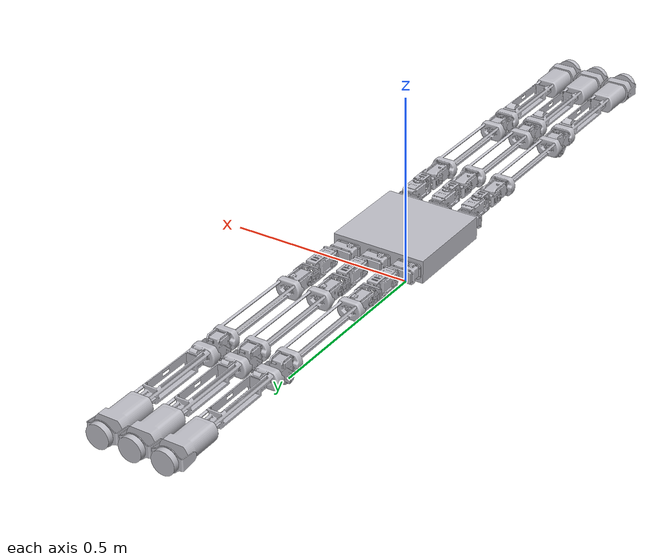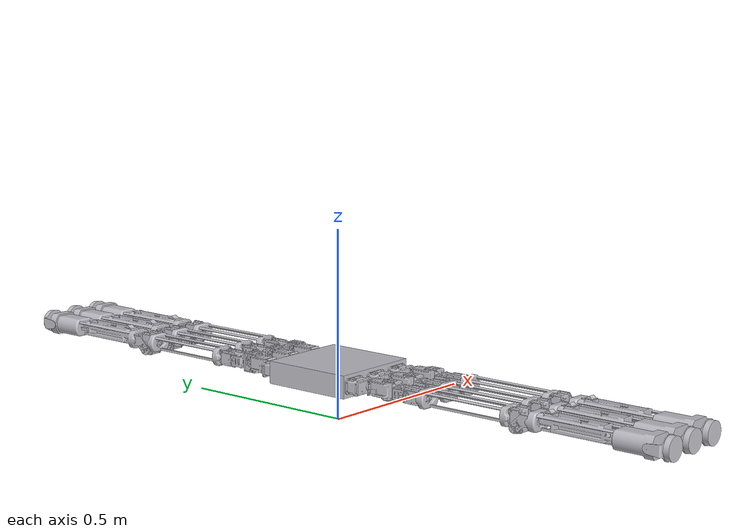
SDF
<sdf version='1.6'>
  <model name='robominer'>
    <link name='base_link'>
      <pose frame=''>0 0 0 0 -0 0</pose>
      <inertial>
        <pose frame=''>0.005574 0 0.129966 0 -0 0</pose>
        <mass>9.84543</mass>
        <inertia>
          <ixx>0.394305</ixx>
          <ixy>-2.50112e-05</ixy>
          <ixz>3.29301e-06</ixz>
          <iyy>0.200688</iyy>
          <iyz>0.000548874</iyz>
          <izz>0.575509</izz>
        </inertia>
      </inertial>
      <collision name='base_link_fixed_joint_lump__cuerpo_collision'>
        <pose frame=''>0 0 0.1 0 -0 0</pose>
        <geometry>
          <mesh>
            <scale>0.001 0.001 0.001</scale>
            <uri>model://robominer_description/meshes/cuerpo.stl</uri>
          </mesh>
        </geometry>
        <surface>
          <contact>
            <ode>
              <kp>1e+06</kp>
              <kd>1</kd>
              <max_vel>0</max_vel>
              <min_depth>0.001</min_depth>
            </ode>
          </contact>
          <friction>
            <ode>
              <mu>0.8</mu>
              <mu2>0.8</mu2>
            </ode>
          </friction>
        </surface>
      </collision>
      <collision name='base_link_fixed_joint_lump__Component1_l_1_collision_1'>
        <pose frame=''>0.100325 0.151 0.13 3.14159 -0 0</pose>
        <geometry>
          <mesh>
            <scale>0.001 0.001 0.001</scale>
            <uri>model://robominer_description/meshes/Component1_1.stl</uri>
          </mesh>
        </geometry>
        <surface>
          <contact>
            <ode>
              <kp>1e+06</kp>
              <kd>1</kd>
              <max_vel>0</max_vel>
              <min_depth>0.001</min_depth>
            </ode>
          </contact>
          <friction>
            <ode>
              <mu>0.8</mu>
              <mu2>0.8</mu2>
            </ode>
          </friction>
        </surface>
      </collision>
      <collision name='base_link_fixed_joint_lump__Component2_l_1_collision_2'>
        <pose frame=''>0.100395 0.151 0.12918 0 -0 3.14159</pose>
        <geometry>
          <mesh>
            <scale>0.001 0.001 0.001</scale>
            <uri>model://robominer_description/meshes/Component2_1.stl</uri>
          </mesh>
        </geometry>
        <surface>
          <contact>
            <ode>
              <kp>1e+06</kp>
              <kd>1</kd>
              <max_vel>0</max_vel>
              <min_depth>0.001</min_depth>
            </ode>
          </contact>
          <friction>
            <ode>
              <mu>0.8</mu>
              <mu2>0.8</mu2>
            </ode>
          </friction>
        </surface>
      </collision>
      <collision name='base_link_fixed_joint_lump__Component3_l_1_collision_3'>
        <pose frame=''>0.100395 0.151 0.12918 0 -0 3.14159</pose>
        <geometry>
          <mesh>
            <scale>0.001 0.001 0.001</scale>
            <uri>model://robominer_description/meshes/Component3_1.stl</uri>
          </mesh>
        </geometry>
        <surface>
          <contact>
            <ode>
              <kp>1e+06</kp>
              <kd>1</kd>
              <max_vel>0</max_vel>
              <min_depth>0.001</min_depth>
            </ode>
          </contact>
          <friction>
            <ode>
              <mu>0.8</mu>
              <mu2>0.8</mu2>
            </ode>
          </friction>
        </surface>
      </collision>
      <collision name='base_link_fixed_joint_lump__Component1_l_2_collision_4'>
        <pose frame=''>0.015325 0.151 0.13 3.14159 -0 0</pose>
        <geometry>
          <mesh>
            <scale>0.001 0.001 0.001</scale>
            <uri>model://robominer_description/meshes/Component1_1.stl</uri>
          </mesh>
        </geometry>
        <surface>
          <contact>
            <ode>
              <kp>1e+06</kp>
              <kd>1</kd>
              <max_vel>0</max_vel>
              <min_depth>0.001</min_depth>
            </ode>
          </contact>
          <friction>
            <ode>
              <mu>0.8</mu>
              <mu2>0.8</mu2>
            </ode>
          </friction>
        </surface>
      </collision>
      <collision name='base_link_fixed_joint_lump__Component2_l_2_collision_5'>
        <pose frame=''>0.015395 0.151 0.12918 0 -0 3.14159</pose>
        <geometry>
          <mesh>
            <scale>0.001 0.001 0.001</scale>
            <uri>model://robominer_description/meshes/Component2_1.stl</uri>
          </mesh>
        </geometry>
        <surface>
          <contact>
            <ode>
              <kp>1e+06</kp>
              <kd>1</kd>
              <max_vel>0</max_vel>
              <min_depth>0.001</min_depth>
            </ode>
          </contact>
          <friction>
            <ode>
              <mu>0.8</mu>
              <mu2>0.8</mu2>
            </ode>
          </friction>
        </surface>
      </collision>
      <collision name='base_link_fixed_joint_lump__Component3_l_2_collision_6'>
        <pose frame=''>0.015395 0.151 0.12918 0 -0 3.14159</pose>
        <geometry>
          <mesh>
            <scale>0.001 0.001 0.001</scale>
            <uri>model://robominer_description/meshes/Component3_1.stl</uri>
          </mesh>
        </geometry>
        <surface>
          <contact>
            <ode>
              <kp>1e+06</kp>
              <kd>1</kd>
              <max_vel>0</max_vel>
              <min_depth>0.001</min_depth>
            </ode>
          </contact>
          <friction>
            <ode>
              <mu>0.8</mu>
              <mu2>0.8</mu2>
            </ode>
          </friction>
        </surface>
      </collision>
      <collision name='base_link_fixed_joint_lump__Component1_l_3_collision_7'>
        <pose frame=''>-0.069675 0.151 0.13 3.14159 -0 0</pose>
        <geometry>
          <mesh>
            <scale>0.001 0.001 0.001</scale>
            <uri>model://robominer_description/meshes/Component1_1.stl</uri>
          </mesh>
        </geometry>
        <surface>
          <contact>
            <ode>
              <kp>1e+06</kp>
              <kd>1</kd>
              <max_vel>0</max_vel>
              <min_depth>0.001</min_depth>
            </ode>
          </contact>
          <friction>
            <ode>
              <mu>0.8</mu>
              <mu2>0.8</mu2>
            </ode>
          </friction>
        </surface>
      </collision>
      <collision name='base_link_fixed_joint_lump__Component2_l_3_collision_8'>
        <pose frame=''>-0.069605 0.151 0.12918 0 -0 3.14159</pose>
        <geometry>
          <mesh>
            <scale>0.001 0.001 0.001</scale>
            <uri>model://robominer_description/meshes/Component2_1.stl</uri>
          </mesh>
        </geometry>
        <surface>
          <contact>
            <ode>
              <kp>1e+06</kp>
              <kd>1</kd>
              <max_vel>0</max_vel>
              <min_depth>0.001</min_depth>
            </ode>
          </contact>
          <friction>
            <ode>
              <mu>0.8</mu>
              <mu2>0.8</mu2>
            </ode>
          </friction>
        </surface>
      </collision>
      <collision name='base_link_fixed_joint_lump__Component3_l_3_collision_9'>
        <pose frame=''>-0.069605 0.151 0.12918 0 -0 3.14159</pose>
        <geometry>
          <mesh>
            <scale>0.001 0.001 0.001</scale>
            <uri>model://robominer_description/meshes/Component3_1.stl</uri>
          </mesh>
        </geometry>
        <surface>
          <contact>
            <ode>
              <kp>1e+06</kp>
              <kd>1</kd>
              <max_vel>0</max_vel>
              <min_depth>0.001</min_depth>
            </ode>
          </contact>
          <friction>
            <ode>
              <mu>0.8</mu>
              <mu2>0.8</mu2>
            </ode>
          </friction>
        </surface>
      </collision>
      <collision name='base_link_fixed_joint_lump__Component1_r_1_collision_10'>
        <pose frame=''>0.100325 -0.151 0.13 0 -0 0</pose>
        <geometry>
          <mesh>
            <scale>0.001 0.001 0.001</scale>
            <uri>model://robominer_description/meshes/Component1_1.stl</uri>
          </mesh>
        </geometry>
        <surface>
          <contact>
            <ode>
              <kp>1e+06</kp>
              <kd>1</kd>
              <max_vel>0</max_vel>
              <min_depth>0.001</min_depth>
            </ode>
          </contact>
          <friction>
            <ode>
              <mu>0.8</mu>
              <mu2>0.8</mu2>
            </ode>
          </friction>
        </surface>
      </collision>
      <collision name='base_link_fixed_joint_lump__Component2_r_1_collision_11'>
        <pose frame=''>0.100325 -0.151 0.13 0 -0 0</pose>
        <geometry>
          <mesh>
            <scale>0.001 0.001 0.001</scale>
            <uri>model://robominer_description/meshes/Component2_1.stl</uri>
          </mesh>
        </geometry>
        <surface>
          <contact>
            <ode>
              <kp>1e+06</kp>
              <kd>1</kd>
              <max_vel>0</max_vel>
              <min_depth>0.001</min_depth>
            </ode>
          </contact>
          <friction>
            <ode>
              <mu>0.8</mu>
              <mu2>0.8</mu2>
            </ode>
          </friction>
        </surface>
      </collision>
      <collision name='base_link_fixed_joint_lump__Component3_r_1_collision_12'>
        <pose frame=''>0.100325 -0.151 0.13 0 -0 0</pose>
        <geometry>
          <mesh>
            <scale>0.001 0.001 0.001</scale>
            <uri>model://robominer_description/meshes/Component3_1.stl</uri>
          </mesh>
        </geometry>
        <surface>
          <contact>
            <ode>
              <kp>1e+06</kp>
              <kd>1</kd>
              <max_vel>0</max_vel>
              <min_depth>0.001</min_depth>
            </ode>
          </contact>
          <friction>
            <ode>
              <mu>0.8</mu>
              <mu2>0.8</mu2>
            </ode>
          </friction>
        </surface>
      </collision>
      <collision name='base_link_fixed_joint_lump__Component1_r_2_collision_13'>
        <pose frame=''>0.015325 -0.151 0.13 0 -0 0</pose>
        <geometry>
          <mesh>
            <scale>0.001 0.001 0.001</scale>
            <uri>model://robominer_description/meshes/Component1_1.stl</uri>
          </mesh>
        </geometry>
        <surface>
          <contact>
            <ode>
              <kp>1e+06</kp>
              <kd>1</kd>
              <max_vel>0</max_vel>
              <min_depth>0.001</min_depth>
            </ode>
          </contact>
          <friction>
            <ode>
              <mu>0.8</mu>
              <mu2>0.8</mu2>
            </ode>
          </friction>
        </surface>
      </collision>
      <collision name='base_link_fixed_joint_lump__Component2_r_2_collision_14'>
        <pose frame=''>0.015325 -0.151 0.13 0 -0 0</pose>
        <geometry>
          <mesh>
            <scale>0.001 0.001 0.001</scale>
            <uri>model://robominer_description/meshes/Component2_1.stl</uri>
          </mesh>
        </geometry>
        <surface>
          <contact>
            <ode>
              <kp>1e+06</kp>
              <kd>1</kd>
              <max_vel>0</max_vel>
              <min_depth>0.001</min_depth>
            </ode>
          </contact>
          <friction>
            <ode>
              <mu>0.8</mu>
              <mu2>0.8</mu2>
            </ode>
          </friction>
        </surface>
      </collision>
      <collision name='base_link_fixed_joint_lump__Component3_r_2_collision_15'>
        <pose frame=''>0.015325 -0.151 0.13 0 -0 0</pose>
        <geometry>
          <mesh>
            <scale>0.001 0.001 0.001</scale>
            <uri>model://robominer_description/meshes/Component3_1.stl</uri>
          </mesh>
        </geometry>
        <surface>
          <contact>
            <ode>
              <kp>1e+06</kp>
              <kd>1</kd>
              <max_vel>0</max_vel>
              <min_depth>0.001</min_depth>
            </ode>
          </contact>
          <friction>
            <ode>
              <mu>0.8</mu>
              <mu2>0.8</mu2>
            </ode>
          </friction>
        </surface>
      </collision>
      <collision name='base_link_fixed_joint_lump__Component1_r_3_collision_16'>
        <pose frame=''>-0.069675 -0.151 0.13 0 -0 0</pose>
        <geometry>
          <mesh>
            <scale>0.001 0.001 0.001</scale>
            <uri>model://robominer_description/meshes/Component1_1.stl</uri>
          </mesh>
        </geometry>
        <surface>
          <contact>
            <ode>
              <kp>1e+06</kp>
              <kd>1</kd>
              <max_vel>0</max_vel>
              <min_depth>0.001</min_depth>
            </ode>
          </contact>
          <friction>
            <ode>
              <mu>0.8</mu>
              <mu2>0.8</mu2>
            </ode>
          </friction>
        </surface>
      </collision>
      <collision name='base_link_fixed_joint_lump__Component2_r_3_collision_17'>
        <pose frame=''>-0.069675 -0.151 0.13 0 -0 0</pose>
        <geometry>
          <mesh>
            <scale>0.001 0.001 0.001</scale>
            <uri>model://robominer_description/meshes/Component2_1.stl</uri>
          </mesh>
        </geometry>
        <surface>
          <contact>
            <ode>
              <kp>1e+06</kp>
              <kd>1</kd>
              <max_vel>0</max_vel>
              <min_depth>0.001</min_depth>
            </ode>
          </contact>
          <friction>
            <ode>
              <mu>0.8</mu>
              <mu2>0.8</mu2>
            </ode>
          </friction>
        </surface>
      </collision>
      <collision name='base_link_fixed_joint_lump__Component3_r_3_collision_18'>
        <pose frame=''>-0.069675 -0.151 0.13 0 -0 0</pose>
        <geometry>
          <mesh>
            <scale>0.001 0.001 0.001</scale>
            <uri>model://robominer_description/meshes/Component3_1.stl</uri>
          </mesh>
        </geometry>
        <surface>
          <contact>
            <ode>
              <kp>1e+06</kp>
              <kd>1</kd>
              <max_vel>0</max_vel>
              <min_depth>0.001</min_depth>
            </ode>
          </contact>
          <friction>
            <ode>
              <mu>0.8</mu>
              <mu2>0.8</mu2>
            </ode>
          </friction>
        </surface>
      </collision>
      <visual name='base_link_fixed_joint_lump__cuerpo_visual'>
        <pose frame=''>0 0 0.1 0 -0 0</pose>
        <geometry>
          <mesh>
            <scale>0.001 0.001 0.001</scale>
            <uri>model://robominer_description/meshes/cuerpo.stl</uri>
          </mesh>
        </geometry>
        <material>
          <script>
            <name>Gazebo/Silver</name>
            <uri>file://media/materials/scripts/gazebo.material</uri>
          </script>
        </material>
      </visual>
      <visual name='base_link_fixed_joint_lump__Component1_l_1_visual_1'>
        <pose frame=''>0.100325 0.151 0.13 3.14159 -0 0</pose>
        <geometry>
          <mesh>
            <scale>0.001 0.001 0.001</scale>
            <uri>model://robominer_description/meshes/Component1_1.stl</uri>
          </mesh>
        </geometry>
        <material>
          <script>
            <name>Gazebo/Silver</name>
            <uri>file://media/materials/scripts/gazebo.material</uri>
          </script>
        </material>
      </visual>
      <visual name='base_link_fixed_joint_lump__Component2_l_1_visual_2'>
        <pose frame=''>0.100395 0.151 0.12918 0 -0 3.14159</pose>
        <geometry>
          <mesh>
            <scale>0.001 0.001 0.001</scale>
            <uri>model://robominer_description/meshes/Component2_1.stl</uri>
          </mesh>
        </geometry>
        <material>
          <script>
            <name>Gazebo/Silver</name>
            <uri>file://media/materials/scripts/gazebo.material</uri>
          </script>
        </material>
      </visual>
      <visual name='base_link_fixed_joint_lump__Component3_l_1_visual_3'>
        <pose frame=''>0.100395 0.151 0.12918 0 -0 3.14159</pose>
        <geometry>
          <mesh>
            <scale>0.001 0.001 0.001</scale>
            <uri>model://robominer_description/meshes/Component3_1.stl</uri>
          </mesh>
        </geometry>
        <material>
          <script>
            <name>Gazebo/Silver</name>
            <uri>file://media/materials/scripts/gazebo.material</uri>
          </script>
        </material>
      </visual>
      <visual name='base_link_fixed_joint_lump__Component1_l_2_visual_4'>
        <pose frame=''>0.015325 0.151 0.13 3.14159 -0 0</pose>
        <geometry>
          <mesh>
            <scale>0.001 0.001 0.001</scale>
            <uri>model://robominer_description/meshes/Component1_1.stl</uri>
          </mesh>
        </geometry>
        <material>
          <script>
            <name>Gazebo/Silver</name>
            <uri>file://media/materials/scripts/gazebo.material</uri>
          </script>
        </material>
      </visual>
      <visual name='base_link_fixed_joint_lump__Component2_l_2_visual_5'>
        <pose frame=''>0.015395 0.151 0.12918 0 -0 3.14159</pose>
        <geometry>
          <mesh>
            <scale>0.001 0.001 0.001</scale>
            <uri>model://robominer_description/meshes/Component2_1.stl</uri>
          </mesh>
        </geometry>
        <material>
          <script>
            <name>Gazebo/Silver</name>
            <uri>file://media/materials/scripts/gazebo.material</uri>
          </script>
        </material>
      </visual>
      <visual name='base_link_fixed_joint_lump__Component3_l_2_visual_6'>
        <pose frame=''>0.015395 0.151 0.12918 0 -0 3.14159</pose>
        <geometry>
          <mesh>
            <scale>0.001 0.001 0.001</scale>
            <uri>model://robominer_description/meshes/Component3_1.stl</uri>
          </mesh>
        </geometry>
        <material>
          <script>
            <name>Gazebo/Silver</name>
            <uri>file://media/materials/scripts/gazebo.material</uri>
          </script>
        </material>
      </visual>
      <visual name='base_link_fixed_joint_lump__Component1_l_3_visual_7'>
        <pose frame=''>-0.069675 0.151 0.13 3.14159 -0 0</pose>
        <geometry>
          <mesh>
            <scale>0.001 0.001 0.001</scale>
            <uri>model://robominer_description/meshes/Component1_1.stl</uri>
          </mesh>
        </geometry>
        <material>
          <script>
            <name>Gazebo/Silver</name>
            <uri>file://media/materials/scripts/gazebo.material</uri>
          </script>
        </material>
      </visual>
      <visual name='base_link_fixed_joint_lump__Component2_l_3_visual_8'>
        <pose frame=''>-0.069605 0.151 0.12918 0 -0 3.14159</pose>
        <geometry>
          <mesh>
            <scale>0.001 0.001 0.001</scale>
            <uri>model://robominer_description/meshes/Component2_1.stl</uri>
          </mesh>
        </geometry>
        <material>
          <script>
            <name>Gazebo/Silver</name>
            <uri>file://media/materials/scripts/gazebo.material</uri>
          </script>
        </material>
      </visual>
      <visual name='base_link_fixed_joint_lump__Component3_l_3_visual_9'>
        <pose frame=''>-0.069605 0.151 0.12918 0 -0 3.14159</pose>
        <geometry>
          <mesh>
            <scale>0.001 0.001 0.001</scale>
            <uri>model://robominer_description/meshes/Component3_1.stl</uri>
          </mesh>
        </geometry>
        <material>
          <script>
            <name>Gazebo/Silver</name>
            <uri>file://media/materials/scripts/gazebo.material</uri>
          </script>
        </material>
      </visual>
      <visual name='base_link_fixed_joint_lump__Component1_r_1_visual_10'>
        <pose frame=''>0.100325 -0.151 0.13 0 -0 0</pose>
        <geometry>
          <mesh>
            <scale>0.001 0.001 0.001</scale>
            <uri>model://robominer_description/meshes/Component1_1.stl</uri>
          </mesh>
        </geometry>
        <material>
          <script>
            <name>Gazebo/Silver</name>
            <uri>file://media/materials/scripts/gazebo.material</uri>
          </script>
        </material>
      </visual>
      <visual name='base_link_fixed_joint_lump__Component2_r_1_visual_11'>
        <pose frame=''>0.100325 -0.151 0.13 0 -0 0</pose>
        <geometry>
          <mesh>
            <scale>0.001 0.001 0.001</scale>
            <uri>model://robominer_description/meshes/Component2_1.stl</uri>
          </mesh>
        </geometry>
        <material>
          <script>
            <name>Gazebo/Silver</name>
            <uri>file://media/materials/scripts/gazebo.material</uri>
          </script>
        </material>
      </visual>
      <visual name='base_link_fixed_joint_lump__Component3_r_1_visual_12'>
        <pose frame=''>0.100325 -0.151 0.13 0 -0 0</pose>
        <geometry>
          <mesh>
            <scale>0.001 0.001 0.001</scale>
            <uri>model://robominer_description/meshes/Component3_1.stl</uri>
          </mesh>
        </geometry>
        <material>
          <script>
            <name>Gazebo/Silver</name>
            <uri>file://media/materials/scripts/gazebo.material</uri>
          </script>
        </material>
      </visual>
      <visual name='base_link_fixed_joint_lump__Component1_r_2_visual_13'>
        <pose frame=''>0.015325 -0.151 0.13 0 -0 0</pose>
        <geometry>
          <mesh>
            <scale>0.001 0.001 0.001</scale>
            <uri>model://robominer_description/meshes/Component1_1.stl</uri>
          </mesh>
        </geometry>
        <material>
          <script>
            <name>Gazebo/Silver</name>
            <uri>file://media/materials/scripts/gazebo.material</uri>
          </script>
        </material>
      </visual>
      <visual name='base_link_fixed_joint_lump__Component2_r_2_visual_14'>
        <pose frame=''>0.015325 -0.151 0.13 0 -0 0</pose>
        <geometry>
          <mesh>
            <scale>0.001 0.001 0.001</scale>
            <uri>model://robominer_description/meshes/Component2_1.stl</uri>
          </mesh>
        </geometry>
        <material>
          <script>
            <name>Gazebo/Silver</name>
            <uri>file://media/materials/scripts/gazebo.material</uri>
          </script>
        </material>
      </visual>
      <visual name='base_link_fixed_joint_lump__Component3_r_2_visual_15'>
        <pose frame=''>0.015325 -0.151 0.13 0 -0 0</pose>
        <geometry>
          <mesh>
            <scale>0.001 0.001 0.001</scale>
            <uri>model://robominer_description/meshes/Component3_1.stl</uri>
          </mesh>
        </geometry>
        <material>
          <script>
            <name>Gazebo/Silver</name>
            <uri>file://media/materials/scripts/gazebo.material</uri>
          </script>
        </material>
      </visual>
      <visual name='base_link_fixed_joint_lump__Component1_r_3_visual_16'>
        <pose frame=''>-0.069675 -0.151 0.13 0 -0 0</pose>
        <geometry>
          <mesh>
            <scale>0.001 0.001 0.001</scale>
            <uri>model://robominer_description/meshes/Component1_1.stl</uri>
          </mesh>
        </geometry>
        <material>
          <script>
            <name>Gazebo/Silver</name>
            <uri>file://media/materials/scripts/gazebo.material</uri>
          </script>
        </material>
      </visual>
      <visual name='base_link_fixed_joint_lump__Component2_r_3_visual_17'>
        <pose frame=''>-0.069675 -0.151 0.13 0 -0 0</pose>
        <geometry>
          <mesh>
            <scale>0.001 0.001 0.001</scale>
            <uri>model://robominer_description/meshes/Component2_1.stl</uri>
          </mesh>
        </geometry>
        <material>
          <script>
            <name>Gazebo/Silver</name>
            <uri>file://media/materials/scripts/gazebo.material</uri>
          </script>
        </material>
      </visual>
      <visual name='base_link_fixed_joint_lump__Component3_r_3_visual_18'>
        <pose frame=''>-0.069675 -0.151 0.13 0 -0 0</pose>
        <geometry>
          <mesh>
            <scale>0.001 0.001 0.001</scale>
            <uri>model://robominer_description/meshes/Component3_1.stl</uri>
          </mesh>
        </geometry>
        <material>
          <script>
            <name>Gazebo/Silver</name>
            <uri>file://media/materials/scripts/gazebo.material</uri>
          </script>
        </material>
      </visual>
      <velocity_decay/>
      <velocity_decay/>
      <velocity_decay/>
      <velocity_decay/>
      <velocity_decay/>
      <velocity_decay/>
      <velocity_decay/>
      <velocity_decay/>
      <velocity_decay/>
      <velocity_decay/>
      <velocity_decay/>
      <velocity_decay/>
      <velocity_decay/>
      <velocity_decay/>
      <velocity_decay/>
      <velocity_decay/>
      <velocity_decay/>
      <gravity>1</gravity>
      <velocity_decay/>
      <gravity>1</gravity>
      <velocity_decay/>
      <self_collide>1</self_collide>
    </link>
    <link name='Component4_l_1'>
      <pose frame=''>0.10036 0.220279 0.153079 0 -0 3.14159</pose>
      <inertial>
        <pose frame=''>0 -0.036 -0.0235 0 -0 0</pose>
        <mass>0.104168</mass>
        <inertia>
          <ixx>5.11669e-05</ixx>
          <ixy>1.40991e-12</ixy>
          <ixz>7.2465e-20</ixz>
          <iyy>5.2e-05</iyy>
          <iyz>-5.73941e-13</iyz>
          <izz>5.11669e-05</izz>
        </inertia>
      </inertial>
      <collision name='Component4_l_1_collision'>
        <pose frame=''>-3.5e-05 0.069279 -0.023899 0 -0 0</pose>
        <geometry>
          <mesh>
            <scale>0.001 0.001 0.001</scale>
            <uri>model://robominer_description/meshes/Component4_1.stl</uri>
          </mesh>
        </geometry>
        <surface>
          <contact>
            <ode>
              <kp>1e+06</kp>
              <kd>1</kd>
              <max_vel>0</max_vel>
              <min_depth>0.001</min_depth>
            </ode>
          </contact>
          <friction>
            <ode>
              <mu>0.8</mu>
              <mu2>0.8</mu2>
            </ode>
          </friction>
        </surface>
      </collision>
      <collision name='Component4_l_1_fixed_joint_lump__Component5_l_1_collision_1'>
        <pose frame=''>-3.5e-05 0.069279 -0.023899 0 -0 0</pose>
        <geometry>
          <mesh>
            <scale>0.001 0.001 0.001</scale>
            <uri>model://robominer_description/meshes/Component5_1.stl</uri>
          </mesh>
        </geometry>
        <surface>
          <contact>
            <ode>
              <kp>1e+06</kp>
              <kd>1</kd>
              <max_vel>0</max_vel>
              <min_depth>0.001</min_depth>
            </ode>
          </contact>
          <friction>
            <ode>
              <mu>0.8</mu>
              <mu2>0.8</mu2>
            </ode>
          </friction>
        </surface>
      </collision>
      <visual name='Component4_l_1_visual'>
        <pose frame=''>-3.5e-05 0.069279 -0.023899 0 -0 0</pose>
        <geometry>
          <mesh>
            <scale>0.001 0.001 0.001</scale>
            <uri>model://robominer_description/meshes/Component4_1.stl</uri>
          </mesh>
        </geometry>
        <material>
          <script>
            <name>Gazebo/Silver</name>
            <uri>file://media/materials/scripts/gazebo.material</uri>
          </script>
        </material>
      </visual>
      <visual name='Component4_l_1_fixed_joint_lump__Component5_l_1_visual_1'>
        <pose frame=''>-3.5e-05 0.069279 -0.023899 0 -0 0</pose>
        <geometry>
          <mesh>
            <scale>0.001 0.001 0.001</scale>
            <uri>model://robominer_description/meshes/Component5_1.stl</uri>
          </mesh>
        </geometry>
        <material>
          <script>
            <name>Gazebo/Silver</name>
            <uri>file://media/materials/scripts/gazebo.material</uri>
          </script>
        </material>
      </visual>
      <velocity_decay/>
      <gravity>1</gravity>
      <velocity_decay/>
      <self_collide>1</self_collide>
    </link>
    <joint name='Rev3_l_1' type='revolute'>
      <child>Component4_l_1</child>
      <parent>base_link</parent>
      <axis>
        <xyz>0 0 1</xyz>
        <limit>
          <lower>-1.91986</lower>
          <upper>1.91986</upper>
          <effort>100</effort>
          <velocity>100</velocity>
        </limit>
        <dynamics>
          <damping>0.1</damping>
          <friction>1</friction>
          <spring_reference>0</spring_reference>
          <spring_stiffness>0</spring_stiffness>
        </dynamics>
        <use_parent_model_frame>1</use_parent_model_frame>
      </axis>
      <physics>
        <provide_feedback>1</provide_feedback>
        <ode>
          <provide_feedback>1</provide_feedback>
          <limit>
            <cfm>0</cfm>
            <erp>0.2</erp>
          </limit>
        </ode>
      </physics>
    </joint>
    <link name='Component6_l_1'>
      <pose frame=''>0.07686 0.292279 0.129579 0 -0 3.14159</pose>
      <inertial>
        <pose frame=''>-0.023547 -0.175176 -0.001507 0 -0 0</pose>
        <mass>1.98279</mass>
        <inertia>
          <ixx>0.0398853</ixx>
          <ixy>-9.86615e-07</ixy>
          <ixz>2.90065e-06</ixz>
          <iyy>0.000870749</iyy>
          <iyz>-0.000622888</iyz>
          <izz>0.0399515</izz>
        </inertia>
      </inertial>
      <collision name='Component6_l_1_collision'>
        <pose frame=''>-0.023535 0.141279 -0.000399 0 -0 0</pose>
        <geometry>
          <mesh>
            <scale>0.001 0.001 0.001</scale>
            <uri>model://robominer_description/meshes/Component6_1.stl</uri>
          </mesh>
        </geometry>
        <surface>
          <contact>
            <ode>
              <kp>1e+06</kp>
              <kd>1</kd>
              <max_vel>0</max_vel>
              <min_depth>0.001</min_depth>
            </ode>
          </contact>
          <friction>
            <ode>
              <mu>0.8</mu>
              <mu2>0.8</mu2>
            </ode>
          </friction>
        </surface>
      </collision>
      <collision name='Component6_l_1_fixed_joint_lump__Component7_l_1_collision_1'>
        <pose frame=''>-0.023535 0.141279 -0.000399 0 -0 0</pose>
        <geometry>
          <mesh>
            <scale>0.001 0.001 0.001</scale>
            <uri>model://robominer_description/meshes/Component7_1.stl</uri>
          </mesh>
        </geometry>
        <surface>
          <contact>
            <ode>
              <kp>1e+06</kp>
              <kd>1</kd>
              <max_vel>0</max_vel>
              <min_depth>0.001</min_depth>
            </ode>
          </contact>
          <friction>
            <ode>
              <mu>0.8</mu>
              <mu2>0.8</mu2>
            </ode>
          </friction>
        </surface>
      </collision>
      <collision name='Component6_l_1_fixed_joint_lump__Component8_l_1_collision_2'>
        <pose frame=''>-0.023535 0.141279 -0.000399 0 -0 0</pose>
        <geometry>
          <mesh>
            <scale>0.001 0.001 0.001</scale>
            <uri>model://robominer_description/meshes/Component8_1.stl</uri>
          </mesh>
        </geometry>
        <surface>
          <contact>
            <ode>
              <kp>1e+06</kp>
              <kd>1</kd>
              <max_vel>0</max_vel>
              <min_depth>0.001</min_depth>
            </ode>
          </contact>
          <friction>
            <ode>
              <mu>0.8</mu>
              <mu2>0.8</mu2>
            </ode>
          </friction>
        </surface>
      </collision>
      <visual name='Component6_l_1_visual'>
        <pose frame=''>-0.023535 0.141279 -0.000399 0 -0 0</pose>
        <geometry>
          <mesh>
            <scale>0.001 0.001 0.001</scale>
            <uri>model://robominer_description/meshes/Component6_1.stl</uri>
          </mesh>
        </geometry>
        <material>
          <script>
            <name>Gazebo/Silver</name>
            <uri>file://media/materials/scripts/gazebo.material</uri>
          </script>
        </material>
      </visual>
      <visual name='Component6_l_1_fixed_joint_lump__Component7_l_1_visual_1'>
        <pose frame=''>-0.023535 0.141279 -0.000399 0 -0 0</pose>
        <geometry>
          <mesh>
            <scale>0.001 0.001 0.001</scale>
            <uri>model://robominer_description/meshes/Component7_1.stl</uri>
          </mesh>
        </geometry>
        <material>
          <script>
            <name>Gazebo/Silver</name>
            <uri>file://media/materials/scripts/gazebo.material</uri>
          </script>
        </material>
      </visual>
      <visual name='Component6_l_1_fixed_joint_lump__Component8_l_1_visual_2'>
        <pose frame=''>-0.023535 0.141279 -0.000399 0 -0 0</pose>
        <geometry>
          <mesh>
            <scale>0.001 0.001 0.001</scale>
            <uri>model://robominer_description/meshes/Component8_1.stl</uri>
          </mesh>
        </geometry>
        <material>
          <script>
            <name>Gazebo/Silver</name>
            <uri>file://media/materials/scripts/gazebo.material</uri>
          </script>
        </material>
      </visual>
      <velocity_decay/>
      <velocity_decay/>
      <gravity>1</gravity>
      <velocity_decay/>
      <self_collide>1</self_collide>
    </link>
    <joint name='Rev5_l_1' type='revolute'>
      <child>Component6_l_1</child>
      <parent>Component4_l_1</parent>
      <axis>
        <xyz>-1 0 0</xyz>
        <limit>
          <lower>-1.91986</lower>
          <upper>1.91986</upper>
          <effort>100</effort>
          <velocity>100</velocity>
        </limit>
        <dynamics>
          <damping>0.1</damping>
          <friction>1</friction>
          <spring_reference>0</spring_reference>
          <spring_stiffness>0</spring_stiffness>
        </dynamics>
        <use_parent_model_frame>1</use_parent_model_frame>
      </axis>
      <physics>
        <provide_feedback>1</provide_feedback>
        <ode>
          <provide_feedback>1</provide_feedback>
          <limit>
            <cfm>0</cfm>
            <erp>0.2</erp>
          </limit>
        </ode>
      </physics>
    </joint>
    <link name='Component9_l_1'>
      <pose frame=''>0.122382 0.622279 0.107579 0 -0 3.14159</pose>
      <inertial>
        <pose frame=''>0.023408 -0.266466 0.022962 0 -0 0</pose>
        <mass>3.75407</mass>
        <inertia>
          <ixx>0.045571</ixx>
          <ixy>-9.18481e-06</ixy>
          <ixz>2.13404e-07</ixz>
          <iyy>0.00185876</iyy>
          <iyz>-0.000505752</iyz>
          <izz>0.0459553</izz>
        </inertia>
      </inertial>
      <collision name='Component9_l_1_collision'>
        <pose frame=''>0.021987 0.471279 0.021601 0 -0 0</pose>
        <geometry>
          <mesh>
            <scale>0.001 0.001 0.001</scale>
            <uri>model://robominer_description/meshes/Component9_1.stl</uri>
          </mesh>
        </geometry>
        <surface>
          <contact>
            <ode>
              <kp>1e+06</kp>
              <kd>1</kd>
              <max_vel>0</max_vel>
              <min_depth>0.001</min_depth>
            </ode>
          </contact>
          <friction>
            <ode>
              <mu>0.8</mu>
              <mu2>0.8</mu2>
            </ode>
          </friction>
        </surface>
      </collision>
      <collision name='Component9_l_1_fixed_joint_lump__Component10_l_1_collision_1'>
        <pose frame=''>0.021987 0.471279 0.021601 0 -0 0</pose>
        <geometry>
          <mesh>
            <scale>0.001 0.001 0.001</scale>
            <uri>model://robominer_description/meshes/Component10_1.stl</uri>
          </mesh>
        </geometry>
        <surface>
          <contact>
            <ode>
              <kp>1e+06</kp>
              <kd>1</kd>
              <max_vel>0</max_vel>
              <min_depth>0.001</min_depth>
            </ode>
          </contact>
          <friction>
            <ode>
              <mu>0.8</mu>
              <mu2>0.8</mu2>
            </ode>
          </friction>
        </surface>
      </collision>
      <collision name='Component9_l_1_fixed_joint_lump__Component11_l_1_collision_2'>
        <pose frame=''>0.021987 0.471279 0.021601 0 -0 0</pose>
        <geometry>
          <mesh>
            <scale>0.001 0.001 0.001</scale>
            <uri>model://robominer_description/meshes/Component11_1.stl</uri>
          </mesh>
        </geometry>
        <surface>
          <contact>
            <ode>
              <kp>1e+06</kp>
              <kd>1</kd>
              <max_vel>0</max_vel>
              <min_depth>0.001</min_depth>
            </ode>
          </contact>
          <friction>
            <ode>
              <mu>0.8</mu>
              <mu2>0.8</mu2>
            </ode>
          </friction>
        </surface>
      </collision>
      <visual name='Component9_l_1_visual'>
        <pose frame=''>0.021987 0.471279 0.021601 0 -0 0</pose>
        <geometry>
          <mesh>
            <scale>0.001 0.001 0.001</scale>
            <uri>model://robominer_description/meshes/Component9_1.stl</uri>
          </mesh>
        </geometry>
        <material>
          <script>
            <name>Gazebo/Silver</name>
            <uri>file://media/materials/scripts/gazebo.material</uri>
          </script>
        </material>
      </visual>
      <visual name='Component9_l_1_fixed_joint_lump__Component10_l_1_visual_1'>
        <pose frame=''>0.021987 0.471279 0.021601 0 -0 0</pose>
        <geometry>
          <mesh>
            <scale>0.001 0.001 0.001</scale>
            <uri>model://robominer_description/meshes/Component10_1.stl</uri>
          </mesh>
        </geometry>
        <material>
          <script>
            <name>Gazebo/Silver</name>
            <uri>file://media/materials/scripts/gazebo.material</uri>
          </script>
        </material>
      </visual>
      <visual name='Component9_l_1_fixed_joint_lump__Component11_l_1_visual_2'>
        <pose frame=''>0.021987 0.471279 0.021601 0 -0 0</pose>
        <geometry>
          <mesh>
            <scale>0.001 0.001 0.001</scale>
            <uri>model://robominer_description/meshes/Component11_1.stl</uri>
          </mesh>
        </geometry>
        <material>
          <script>
            <name>Gazebo/Silver</name>
            <uri>file://media/materials/scripts/gazebo.material</uri>
          </script>
        </material>
      </visual>
      <velocity_decay/>
      <velocity_decay/>
      <gravity>1</gravity>
      <velocity_decay/>
      <self_collide>1</self_collide>
    </link>
    <joint name='Rev8_l_1' type='revolute'>
      <child>Component9_l_1</child>
      <parent>Component6_l_1</parent>
      <axis>
        <xyz>-1 0 0</xyz>
        <limit>
          <lower>-0.785398</lower>
          <upper>3.14159</upper>
          <effort>100</effort>
          <velocity>100</velocity>
        </limit>
        <dynamics>
          <damping>0.1</damping>
          <friction>1</friction>
          <spring_reference>0</spring_reference>
          <spring_stiffness>0</spring_stiffness>
        </dynamics>
        <use_parent_model_frame>1</use_parent_model_frame>
      </axis>
      <physics>
        <provide_feedback>1</provide_feedback>
        <ode>
          <provide_feedback>1</provide_feedback>
          <limit>
            <cfm>0</cfm>
            <erp>0.2</erp>
          </limit>
        </ode>
      </physics>
    </joint>
    <link name='Component12_l_1'>
      <pose frame=''>0.062967 0.99117 0.129943 0 -0 3.14159</pose>
      <inertial>
        <pose frame=''>-0.036122 -0.038163 -0 0 -0 0</pose>
        <mass>0.430074</mass>
        <inertia>
          <ixx>0.000136</ixx>
          <ixy>0</ixy>
          <ixz>0</ixz>
          <iyy>0.000245</iyy>
          <iyz>0</iyz>
          <izz>0.000199</izz>
        </inertia>
      </inertial>
      <collision name='Component12_l_1_collision'>
        <pose frame=''>-0.037428 0.84017 -0.000763 0 -0 0</pose>
        <geometry>
          <mesh>
            <scale>0.001 0.001 0.001</scale>
            <uri>model://robominer_description/meshes/Component12_1.stl</uri>
          </mesh>
        </geometry>
        <surface>
          <contact>
            <ode>
              <kp>1e+06</kp>
              <kd>1</kd>
              <max_vel>0</max_vel>
              <min_depth>0.001</min_depth>
            </ode>
          </contact>
          <friction>
            <ode>
              <mu>0.8</mu>
              <mu2>0.8</mu2>
            </ode>
          </friction>
        </surface>
      </collision>
      <visual name='Component12_l_1_visual'>
        <pose frame=''>-0.037428 0.84017 -0.000763 0 -0 0</pose>
        <geometry>
          <mesh>
            <scale>0.001 0.001 0.001</scale>
            <uri>model://robominer_description/meshes/Component12_1.stl</uri>
          </mesh>
        </geometry>
        <material>
          <script>
            <name>Gazebo/Silver</name>
            <uri>file://media/materials/scripts/gazebo.material</uri>
          </script>
        </material>
      </visual>
      <gravity>1</gravity>
      <velocity_decay/>
      <self_collide>1</self_collide>
    </link>
    <joint name='Rev11_l_1' type='revolute'>
      <child>Component12_l_1</child>
      <parent>Component9_l_1</parent>
      <axis>
        <xyz>-1 0 0</xyz>
        <limit>
          <lower>-1.5708</lower>
          <upper>1.5708</upper>
          <effort>100</effort>
          <velocity>100</velocity>
        </limit>
        <dynamics>
          <damping>0.1</damping>
          <friction>1</friction>
          <spring_reference>0</spring_reference>
          <spring_stiffness>0</spring_stiffness>
        </dynamics>
        <use_parent_model_frame>1</use_parent_model_frame>
      </axis>
      <physics>
        <provide_feedback>1</provide_feedback>
        <ode>
          <provide_feedback>1</provide_feedback>
          <limit>
            <cfm>0</cfm>
            <erp>0.2</erp>
          </limit>
        </ode>
      </physics>
    </joint>
    <link name='Component4_l_2'>
      <pose frame=''>0.01536 0.220279 0.153079 0 -0 3.14159</pose>
      <inertial>
        <pose frame=''>0 -0.036 -0.0235 0 -0 0</pose>
        <mass>0.104168</mass>
        <inertia>
          <ixx>5.11669e-05</ixx>
          <ixy>1.40991e-12</ixy>
          <ixz>7.2465e-20</ixz>
          <iyy>5.2e-05</iyy>
          <iyz>-5.73941e-13</iyz>
          <izz>5.11669e-05</izz>
        </inertia>
      </inertial>
      <collision name='Component4_l_2_collision'>
        <pose frame=''>-3.5e-05 0.069279 -0.023899 0 -0 0</pose>
        <geometry>
          <mesh>
            <scale>0.001 0.001 0.001</scale>
            <uri>model://robominer_description/meshes/Component4_1.stl</uri>
          </mesh>
        </geometry>
        <surface>
          <contact>
            <ode>
              <kp>1e+06</kp>
              <kd>1</kd>
              <max_vel>0</max_vel>
              <min_depth>0.001</min_depth>
            </ode>
          </contact>
          <friction>
            <ode>
              <mu>0.8</mu>
              <mu2>0.8</mu2>
            </ode>
          </friction>
        </surface>
      </collision>
      <collision name='Component4_l_2_fixed_joint_lump__Component5_l_2_collision_1'>
        <pose frame=''>-3.5e-05 0.069279 -0.023899 0 -0 0</pose>
        <geometry>
          <mesh>
            <scale>0.001 0.001 0.001</scale>
            <uri>model://robominer_description/meshes/Component5_1.stl</uri>
          </mesh>
        </geometry>
        <surface>
          <contact>
            <ode>
              <kp>1e+06</kp>
              <kd>1</kd>
              <max_vel>0</max_vel>
              <min_depth>0.001</min_depth>
            </ode>
          </contact>
          <friction>
            <ode>
              <mu>0.8</mu>
              <mu2>0.8</mu2>
            </ode>
          </friction>
        </surface>
      </collision>
      <visual name='Component4_l_2_visual'>
        <pose frame=''>-3.5e-05 0.069279 -0.023899 0 -0 0</pose>
        <geometry>
          <mesh>
            <scale>0.001 0.001 0.001</scale>
            <uri>model://robominer_description/meshes/Component4_1.stl</uri>
          </mesh>
        </geometry>
        <material>
          <script>
            <name>Gazebo/Silver</name>
            <uri>file://media/materials/scripts/gazebo.material</uri>
          </script>
        </material>
      </visual>
      <visual name='Component4_l_2_fixed_joint_lump__Component5_l_2_visual_1'>
        <pose frame=''>-3.5e-05 0.069279 -0.023899 0 -0 0</pose>
        <geometry>
          <mesh>
            <scale>0.001 0.001 0.001</scale>
            <uri>model://robominer_description/meshes/Component5_1.stl</uri>
          </mesh>
        </geometry>
        <material>
          <script>
            <name>Gazebo/Silver</name>
            <uri>file://media/materials/scripts/gazebo.material</uri>
          </script>
        </material>
      </visual>
      <velocity_decay/>
      <gravity>1</gravity>
      <velocity_decay/>
      <self_collide>1</self_collide>
    </link>
    <joint name='Rev3_l_2' type='revolute'>
      <child>Component4_l_2</child>
      <parent>base_link</parent>
      <axis>
        <xyz>0 0 1</xyz>
        <limit>
          <lower>-1.91986</lower>
          <upper>1.91986</upper>
          <effort>100</effort>
          <velocity>100</velocity>
        </limit>
        <dynamics>
          <damping>0.1</damping>
          <friction>1</friction>
          <spring_reference>0</spring_reference>
          <spring_stiffness>0</spring_stiffness>
        </dynamics>
        <use_parent_model_frame>1</use_parent_model_frame>
      </axis>
      <physics>
        <provide_feedback>1</provide_feedback>
        <ode>
          <provide_feedback>1</provide_feedback>
          <limit>
            <cfm>0</cfm>
            <erp>0.2</erp>
          </limit>
        </ode>
      </physics>
    </joint>
    <link name='Component6_l_2'>
      <pose frame=''>-0.00814 0.292279 0.129579 0 -0 3.14159</pose>
      <inertial>
        <pose frame=''>-0.023547 -0.175176 -0.001507 0 -0 0</pose>
        <mass>1.98279</mass>
        <inertia>
          <ixx>0.0398853</ixx>
          <ixy>-9.86615e-07</ixy>
          <ixz>2.90065e-06</ixz>
          <iyy>0.000870749</iyy>
          <iyz>-0.000622888</iyz>
          <izz>0.0399515</izz>
        </inertia>
      </inertial>
      <collision name='Component6_l_2_collision'>
        <pose frame=''>-0.023535 0.141279 -0.000399 0 -0 0</pose>
        <geometry>
          <mesh>
            <scale>0.001 0.001 0.001</scale>
            <uri>model://robominer_description/meshes/Component6_1.stl</uri>
          </mesh>
        </geometry>
        <surface>
          <contact>
            <ode>
              <kp>1e+06</kp>
              <kd>1</kd>
              <max_vel>0</max_vel>
              <min_depth>0.001</min_depth>
            </ode>
          </contact>
          <friction>
            <ode>
              <mu>0.8</mu>
              <mu2>0.8</mu2>
            </ode>
          </friction>
        </surface>
      </collision>
      <collision name='Component6_l_2_fixed_joint_lump__Component7_l_2_collision_1'>
        <pose frame=''>-0.023535 0.141279 -0.000399 0 -0 0</pose>
        <geometry>
          <mesh>
            <scale>0.001 0.001 0.001</scale>
            <uri>model://robominer_description/meshes/Component7_1.stl</uri>
          </mesh>
        </geometry>
        <surface>
          <contact>
            <ode>
              <kp>1e+06</kp>
              <kd>1</kd>
              <max_vel>0</max_vel>
              <min_depth>0.001</min_depth>
            </ode>
          </contact>
          <friction>
            <ode>
              <mu>0.8</mu>
              <mu2>0.8</mu2>
            </ode>
          </friction>
        </surface>
      </collision>
      <collision name='Component6_l_2_fixed_joint_lump__Component8_l_2_collision_2'>
        <pose frame=''>-0.023535 0.141279 -0.000399 0 -0 0</pose>
        <geometry>
          <mesh>
            <scale>0.001 0.001 0.001</scale>
            <uri>model://robominer_description/meshes/Component8_1.stl</uri>
          </mesh>
        </geometry>
        <surface>
          <contact>
            <ode>
              <kp>1e+06</kp>
              <kd>1</kd>
              <max_vel>0</max_vel>
              <min_depth>0.001</min_depth>
            </ode>
          </contact>
          <friction>
            <ode>
              <mu>0.8</mu>
              <mu2>0.8</mu2>
            </ode>
          </friction>
        </surface>
      </collision>
      <visual name='Component6_l_2_visual'>
        <pose frame=''>-0.023535 0.141279 -0.000399 0 -0 0</pose>
        <geometry>
          <mesh>
            <scale>0.001 0.001 0.001</scale>
            <uri>model://robominer_description/meshes/Component6_1.stl</uri>
          </mesh>
        </geometry>
        <material>
          <script>
            <name>Gazebo/Silver</name>
            <uri>file://media/materials/scripts/gazebo.material</uri>
          </script>
        </material>
      </visual>
      <visual name='Component6_l_2_fixed_joint_lump__Component7_l_2_visual_1'>
        <pose frame=''>-0.023535 0.141279 -0.000399 0 -0 0</pose>
        <geometry>
          <mesh>
            <scale>0.001 0.001 0.001</scale>
            <uri>model://robominer_description/meshes/Component7_1.stl</uri>
          </mesh>
        </geometry>
        <material>
          <script>
            <name>Gazebo/Silver</name>
            <uri>file://media/materials/scripts/gazebo.material</uri>
          </script>
        </material>
      </visual>
      <visual name='Component6_l_2_fixed_joint_lump__Component8_l_2_visual_2'>
        <pose frame=''>-0.023535 0.141279 -0.000399 0 -0 0</pose>
        <geometry>
          <mesh>
            <scale>0.001 0.001 0.001</scale>
            <uri>model://robominer_description/meshes/Component8_1.stl</uri>
          </mesh>
        </geometry>
        <material>
          <script>
            <name>Gazebo/Silver</name>
            <uri>file://media/materials/scripts/gazebo.material</uri>
          </script>
        </material>
      </visual>
      <velocity_decay/>
      <velocity_decay/>
      <gravity>1</gravity>
      <velocity_decay/>
      <self_collide>1</self_collide>
    </link>
    <joint name='Rev5_l_2' type='revolute'>
      <child>Component6_l_2</child>
      <parent>Component4_l_2</parent>
      <axis>
        <xyz>-1 0 0</xyz>
        <limit>
          <lower>-1.91986</lower>
          <upper>1.91986</upper>
          <effort>100</effort>
          <velocity>100</velocity>
        </limit>
        <dynamics>
          <damping>0.1</damping>
          <friction>1</friction>
          <spring_reference>0</spring_reference>
          <spring_stiffness>0</spring_stiffness>
        </dynamics>
        <use_parent_model_frame>1</use_parent_model_frame>
      </axis>
      <physics>
        <provide_feedback>1</provide_feedback>
        <ode>
          <provide_feedback>1</provide_feedback>
          <limit>
            <cfm>0</cfm>
            <erp>0.2</erp>
          </limit>
        </ode>
      </physics>
    </joint>
    <link name='Component9_l_2'>
      <pose frame=''>0.037382 0.622279 0.107579 0 -0 3.14159</pose>
      <inertial>
        <pose frame=''>0.023408 -0.266466 0.022962 0 -0 0</pose>
        <mass>3.75407</mass>
        <inertia>
          <ixx>0.045571</ixx>
          <ixy>-9.18481e-06</ixy>
          <ixz>2.13404e-07</ixz>
          <iyy>0.00185876</iyy>
          <iyz>-0.000505752</iyz>
          <izz>0.0459553</izz>
        </inertia>
      </inertial>
      <collision name='Component9_l_2_collision'>
        <pose frame=''>0.021987 0.471279 0.021601 0 -0 0</pose>
        <geometry>
          <mesh>
            <scale>0.001 0.001 0.001</scale>
            <uri>model://robominer_description/meshes/Component9_1.stl</uri>
          </mesh>
        </geometry>
        <surface>
          <contact>
            <ode>
              <kp>1e+06</kp>
              <kd>1</kd>
              <max_vel>0</max_vel>
              <min_depth>0.001</min_depth>
            </ode>
          </contact>
          <friction>
            <ode>
              <mu>0.8</mu>
              <mu2>0.8</mu2>
            </ode>
          </friction>
        </surface>
      </collision>
      <collision name='Component9_l_2_fixed_joint_lump__Component10_l_2_collision_1'>
        <pose frame=''>0.021987 0.471279 0.021601 0 -0 0</pose>
        <geometry>
          <mesh>
            <scale>0.001 0.001 0.001</scale>
            <uri>model://robominer_description/meshes/Component10_1.stl</uri>
          </mesh>
        </geometry>
        <surface>
          <contact>
            <ode>
              <kp>1e+06</kp>
              <kd>1</kd>
              <max_vel>0</max_vel>
              <min_depth>0.001</min_depth>
            </ode>
          </contact>
          <friction>
            <ode>
              <mu>0.8</mu>
              <mu2>0.8</mu2>
            </ode>
          </friction>
        </surface>
      </collision>
      <collision name='Component9_l_2_fixed_joint_lump__Component11_l_2_collision_2'>
        <pose frame=''>0.021987 0.471279 0.021601 0 -0 0</pose>
        <geometry>
          <mesh>
            <scale>0.001 0.001 0.001</scale>
            <uri>model://robominer_description/meshes/Component11_1.stl</uri>
          </mesh>
        </geometry>
        <surface>
          <contact>
            <ode>
              <kp>1e+06</kp>
              <kd>1</kd>
              <max_vel>0</max_vel>
              <min_depth>0.001</min_depth>
            </ode>
          </contact>
          <friction>
            <ode>
              <mu>0.8</mu>
              <mu2>0.8</mu2>
            </ode>
          </friction>
        </surface>
      </collision>
      <visual name='Component9_l_2_visual'>
        <pose frame=''>0.021987 0.471279 0.021601 0 -0 0</pose>
        <geometry>
          <mesh>
            <scale>0.001 0.001 0.001</scale>
            <uri>model://robominer_description/meshes/Component9_1.stl</uri>
          </mesh>
        </geometry>
        <material>
          <script>
            <name>Gazebo/Silver</name>
            <uri>file://media/materials/scripts/gazebo.material</uri>
          </script>
        </material>
      </visual>
      <visual name='Component9_l_2_fixed_joint_lump__Component10_l_2_visual_1'>
        <pose frame=''>0.021987 0.471279 0.021601 0 -0 0</pose>
        <geometry>
          <mesh>
            <scale>0.001 0.001 0.001</scale>
            <uri>model://robominer_description/meshes/Component10_1.stl</uri>
          </mesh>
        </geometry>
        <material>
          <script>
            <name>Gazebo/Silver</name>
            <uri>file://media/materials/scripts/gazebo.material</uri>
          </script>
        </material>
      </visual>
      <visual name='Component9_l_2_fixed_joint_lump__Component11_l_2_visual_2'>
        <pose frame=''>0.021987 0.471279 0.021601 0 -0 0</pose>
        <geometry>
          <mesh>
            <scale>0.001 0.001 0.001</scale>
            <uri>model://robominer_description/meshes/Component11_1.stl</uri>
          </mesh>
        </geometry>
        <material>
          <script>
            <name>Gazebo/Silver</name>
            <uri>file://media/materials/scripts/gazebo.material</uri>
          </script>
        </material>
      </visual>
      <velocity_decay/>
      <velocity_decay/>
      <gravity>1</gravity>
      <velocity_decay/>
      <self_collide>1</self_collide>
    </link>
    <joint name='Rev8_l_2' type='revolute'>
      <child>Component9_l_2</child>
      <parent>Component6_l_2</parent>
      <axis>
        <xyz>-1 0 0</xyz>
        <limit>
          <lower>-0.785398</lower>
          <upper>3.14159</upper>
          <effort>100</effort>
          <velocity>100</velocity>
        </limit>
        <dynamics>
          <damping>0.1</damping>
          <friction>1</friction>
          <spring_reference>0</spring_reference>
          <spring_stiffness>0</spring_stiffness>
        </dynamics>
        <use_parent_model_frame>1</use_parent_model_frame>
      </axis>
      <physics>
        <provide_feedback>1</provide_feedback>
        <ode>
          <provide_feedback>1</provide_feedback>
          <limit>
            <cfm>0</cfm>
            <erp>0.2</erp>
          </limit>
        </ode>
      </physics>
    </joint>
    <link name='Component12_l_2'>
      <pose frame=''>-0.022033 0.99117 0.129943 0 -0 3.14159</pose>
      <inertial>
        <pose frame=''>-0.036122 -0.038163 -0 0 -0 0</pose>
        <mass>0.430074</mass>
        <inertia>
          <ixx>0.000136</ixx>
          <ixy>0</ixy>
          <ixz>0</ixz>
          <iyy>0.000245</iyy>
          <iyz>0</iyz>
          <izz>0.000199</izz>
        </inertia>
      </inertial>
      <collision name='Component12_l_2_collision'>
        <pose frame=''>-0.037428 0.84017 -0.000763 0 -0 0</pose>
        <geometry>
          <mesh>
            <scale>0.001 0.001 0.001</scale>
            <uri>model://robominer_description/meshes/Component12_1.stl</uri>
          </mesh>
        </geometry>
        <surface>
          <contact>
            <ode>
              <kp>1e+06</kp>
              <kd>1</kd>
              <max_vel>0</max_vel>
              <min_depth>0.001</min_depth>
            </ode>
          </contact>
          <friction>
            <ode>
              <mu>0.8</mu>
              <mu2>0.8</mu2>
            </ode>
          </friction>
        </surface>
      </collision>
      <visual name='Component12_l_2_visual'>
        <pose frame=''>-0.037428 0.84017 -0.000763 0 -0 0</pose>
        <geometry>
          <mesh>
            <scale>0.001 0.001 0.001</scale>
            <uri>model://robominer_description/meshes/Component12_1.stl</uri>
          </mesh>
        </geometry>
        <material>
          <script>
            <name>Gazebo/Silver</name>
            <uri>file://media/materials/scripts/gazebo.material</uri>
          </script>
        </material>
      </visual>
      <gravity>1</gravity>
      <velocity_decay/>
      <self_collide>1</self_collide>
    </link>
    <joint name='Rev11_l_2' type='revolute'>
      <child>Component12_l_2</child>
      <parent>Component9_l_2</parent>
      <axis>
        <xyz>-1 0 0</xyz>
        <limit>
          <lower>-1.5708</lower>
          <upper>1.5708</upper>
          <effort>100</effort>
          <velocity>100</velocity>
        </limit>
        <dynamics>
          <damping>0.1</damping>
          <friction>1</friction>
          <spring_reference>0</spring_reference>
          <spring_stiffness>0</spring_stiffness>
        </dynamics>
        <use_parent_model_frame>1</use_parent_model_frame>
      </axis>
      <physics>
        <provide_feedback>1</provide_feedback>
        <ode>
          <provide_feedback>1</provide_feedback>
          <limit>
            <cfm>0</cfm>
            <erp>0.2</erp>
          </limit>
        </ode>
      </physics>
    </joint>
    <link name='Component4_l_3'>
      <pose frame=''>-0.06964 0.220279 0.153079 0 -0 3.14159</pose>
      <inertial>
        <pose frame=''>0 -0.036 -0.0235 0 -0 0</pose>
        <mass>0.104168</mass>
        <inertia>
          <ixx>5.11669e-05</ixx>
          <ixy>1.40991e-12</ixy>
          <ixz>7.2465e-20</ixz>
          <iyy>5.2e-05</iyy>
          <iyz>-5.73941e-13</iyz>
          <izz>5.11669e-05</izz>
        </inertia>
      </inertial>
      <collision name='Component4_l_3_collision'>
        <pose frame=''>-3.5e-05 0.069279 -0.023899 0 -0 0</pose>
        <geometry>
          <mesh>
            <scale>0.001 0.001 0.001</scale>
            <uri>model://robominer_description/meshes/Component4_1.stl</uri>
          </mesh>
        </geometry>
        <surface>
          <contact>
            <ode>
              <kp>1e+06</kp>
              <kd>1</kd>
              <max_vel>0</max_vel>
              <min_depth>0.001</min_depth>
            </ode>
          </contact>
          <friction>
            <ode>
              <mu>0.8</mu>
              <mu2>0.8</mu2>
            </ode>
          </friction>
        </surface>
      </collision>
      <collision name='Component4_l_3_fixed_joint_lump__Component5_l_3_collision_1'>
        <pose frame=''>-3.5e-05 0.069279 -0.023899 0 -0 0</pose>
        <geometry>
          <mesh>
            <scale>0.001 0.001 0.001</scale>
            <uri>model://robominer_description/meshes/Component5_1.stl</uri>
          </mesh>
        </geometry>
        <surface>
          <contact>
            <ode>
              <kp>1e+06</kp>
              <kd>1</kd>
              <max_vel>0</max_vel>
              <min_depth>0.001</min_depth>
            </ode>
          </contact>
          <friction>
            <ode>
              <mu>0.8</mu>
              <mu2>0.8</mu2>
            </ode>
          </friction>
        </surface>
      </collision>
      <visual name='Component4_l_3_visual'>
        <pose frame=''>-3.5e-05 0.069279 -0.023899 0 -0 0</pose>
        <geometry>
          <mesh>
            <scale>0.001 0.001 0.001</scale>
            <uri>model://robominer_description/meshes/Component4_1.stl</uri>
          </mesh>
        </geometry>
        <material>
          <script>
            <name>Gazebo/Silver</name>
            <uri>file://media/materials/scripts/gazebo.material</uri>
          </script>
        </material>
      </visual>
      <visual name='Component4_l_3_fixed_joint_lump__Component5_l_3_visual_1'>
        <pose frame=''>-3.5e-05 0.069279 -0.023899 0 -0 0</pose>
        <geometry>
          <mesh>
            <scale>0.001 0.001 0.001</scale>
            <uri>model://robominer_description/meshes/Component5_1.stl</uri>
          </mesh>
        </geometry>
        <material>
          <script>
            <name>Gazebo/Silver</name>
            <uri>file://media/materials/scripts/gazebo.material</uri>
          </script>
        </material>
      </visual>
      <velocity_decay/>
      <gravity>1</gravity>
      <velocity_decay/>
      <self_collide>1</self_collide>
    </link>
    <joint name='Rev3_l_3' type='revolute'>
      <child>Component4_l_3</child>
      <parent>base_link</parent>
      <axis>
        <xyz>0 0 1</xyz>
        <limit>
          <lower>-1.91986</lower>
          <upper>1.91986</upper>
          <effort>100</effort>
          <velocity>100</velocity>
        </limit>
        <dynamics>
          <damping>0.1</damping>
          <friction>1</friction>
          <spring_reference>0</spring_reference>
          <spring_stiffness>0</spring_stiffness>
        </dynamics>
        <use_parent_model_frame>1</use_parent_model_frame>
      </axis>
      <physics>
        <provide_feedback>1</provide_feedback>
        <ode>
          <provide_feedback>1</provide_feedback>
          <limit>
            <cfm>0</cfm>
            <erp>0.2</erp>
          </limit>
        </ode>
      </physics>
    </joint>
    <link name='Component6_l_3'>
      <pose frame=''>-0.09314 0.292279 0.129579 0 -0 3.14159</pose>
      <inertial>
        <pose frame=''>-0.023547 -0.175176 -0.001507 0 -0 0</pose>
        <mass>1.98279</mass>
        <inertia>
          <ixx>0.0398853</ixx>
          <ixy>-9.86615e-07</ixy>
          <ixz>2.90065e-06</ixz>
          <iyy>0.000870749</iyy>
          <iyz>-0.000622888</iyz>
          <izz>0.0399515</izz>
        </inertia>
      </inertial>
      <collision name='Component6_l_3_collision'>
        <pose frame=''>-0.023535 0.141279 -0.000399 0 -0 0</pose>
        <geometry>
          <mesh>
            <scale>0.001 0.001 0.001</scale>
            <uri>model://robominer_description/meshes/Component6_1.stl</uri>
          </mesh>
        </geometry>
        <surface>
          <contact>
            <ode>
              <kp>1e+06</kp>
              <kd>1</kd>
              <max_vel>0</max_vel>
              <min_depth>0.001</min_depth>
            </ode>
          </contact>
          <friction>
            <ode>
              <mu>0.8</mu>
              <mu2>0.8</mu2>
            </ode>
          </friction>
        </surface>
      </collision>
      <collision name='Component6_l_3_fixed_joint_lump__Component7_l_3_collision_1'>
        <pose frame=''>-0.023535 0.141279 -0.000399 0 -0 0</pose>
        <geometry>
          <mesh>
            <scale>0.001 0.001 0.001</scale>
            <uri>model://robominer_description/meshes/Component7_1.stl</uri>
          </mesh>
        </geometry>
        <surface>
          <contact>
            <ode>
              <kp>1e+06</kp>
              <kd>1</kd>
              <max_vel>0</max_vel>
              <min_depth>0.001</min_depth>
            </ode>
          </contact>
          <friction>
            <ode>
              <mu>0.8</mu>
              <mu2>0.8</mu2>
            </ode>
          </friction>
        </surface>
      </collision>
      <collision name='Component6_l_3_fixed_joint_lump__Component8_l_3_collision_2'>
        <pose frame=''>-0.023535 0.141279 -0.000399 0 -0 0</pose>
        <geometry>
          <mesh>
            <scale>0.001 0.001 0.001</scale>
            <uri>model://robominer_description/meshes/Component8_1.stl</uri>
          </mesh>
        </geometry>
        <surface>
          <contact>
            <ode>
              <kp>1e+06</kp>
              <kd>1</kd>
              <max_vel>0</max_vel>
              <min_depth>0.001</min_depth>
            </ode>
          </contact>
          <friction>
            <ode>
              <mu>0.8</mu>
              <mu2>0.8</mu2>
            </ode>
          </friction>
        </surface>
      </collision>
      <visual name='Component6_l_3_visual'>
        <pose frame=''>-0.023535 0.141279 -0.000399 0 -0 0</pose>
        <geometry>
          <mesh>
            <scale>0.001 0.001 0.001</scale>
            <uri>model://robominer_description/meshes/Component6_1.stl</uri>
          </mesh>
        </geometry>
        <material>
          <script>
            <name>Gazebo/Silver</name>
            <uri>file://media/materials/scripts/gazebo.material</uri>
          </script>
        </material>
      </visual>
      <visual name='Component6_l_3_fixed_joint_lump__Component7_l_3_visual_1'>
        <pose frame=''>-0.023535 0.141279 -0.000399 0 -0 0</pose>
        <geometry>
          <mesh>
            <scale>0.001 0.001 0.001</scale>
            <uri>model://robominer_description/meshes/Component7_1.stl</uri>
          </mesh>
        </geometry>
        <material>
          <script>
            <name>Gazebo/Silver</name>
            <uri>file://media/materials/scripts/gazebo.material</uri>
          </script>
        </material>
      </visual>
      <visual name='Component6_l_3_fixed_joint_lump__Component8_l_3_visual_2'>
        <pose frame=''>-0.023535 0.141279 -0.000399 0 -0 0</pose>
        <geometry>
          <mesh>
            <scale>0.001 0.001 0.001</scale>
            <uri>model://robominer_description/meshes/Component8_1.stl</uri>
          </mesh>
        </geometry>
        <material>
          <script>
            <name>Gazebo/Silver</name>
            <uri>file://media/materials/scripts/gazebo.material</uri>
          </script>
        </material>
      </visual>
      <velocity_decay/>
      <velocity_decay/>
      <gravity>1</gravity>
      <velocity_decay/>
      <self_collide>1</self_collide>
    </link>
    <joint name='Rev5_l_3' type='revolute'>
      <child>Component6_l_3</child>
      <parent>Component4_l_3</parent>
      <axis>
        <xyz>-1 0 0</xyz>
        <limit>
          <lower>-1.91986</lower>
          <upper>1.91986</upper>
          <effort>100</effort>
          <velocity>100</velocity>
        </limit>
        <dynamics>
          <damping>0.1</damping>
          <friction>1</friction>
          <spring_reference>0</spring_reference>
          <spring_stiffness>0</spring_stiffness>
        </dynamics>
        <use_parent_model_frame>1</use_parent_model_frame>
      </axis>
      <physics>
        <provide_feedback>1</provide_feedback>
        <ode>
          <provide_feedback>1</provide_feedback>
          <limit>
            <cfm>0</cfm>
            <erp>0.2</erp>
          </limit>
        </ode>
      </physics>
    </joint>
    <link name='Component9_l_3'>
      <pose frame=''>-0.047618 0.622279 0.107579 0 -0 3.14159</pose>
      <inertial>
        <pose frame=''>0.023408 -0.266466 0.022962 0 -0 0</pose>
        <mass>3.75407</mass>
        <inertia>
          <ixx>0.045571</ixx>
          <ixy>-9.18481e-06</ixy>
          <ixz>2.13404e-07</ixz>
          <iyy>0.00185876</iyy>
          <iyz>-0.000505752</iyz>
          <izz>0.0459553</izz>
        </inertia>
      </inertial>
      <collision name='Component9_l_3_collision'>
        <pose frame=''>0.021987 0.471279 0.021601 0 -0 0</pose>
        <geometry>
          <mesh>
            <scale>0.001 0.001 0.001</scale>
            <uri>model://robominer_description/meshes/Component9_1.stl</uri>
          </mesh>
        </geometry>
        <surface>
          <contact>
            <ode>
              <kp>1e+06</kp>
              <kd>1</kd>
              <max_vel>0</max_vel>
              <min_depth>0.001</min_depth>
            </ode>
          </contact>
          <friction>
            <ode>
              <mu>0.8</mu>
              <mu2>0.8</mu2>
            </ode>
          </friction>
        </surface>
      </collision>
      <collision name='Component9_l_3_fixed_joint_lump__Component10_l_3_collision_1'>
        <pose frame=''>0.021987 0.471279 0.021601 0 -0 0</pose>
        <geometry>
          <mesh>
            <scale>0.001 0.001 0.001</scale>
            <uri>model://robominer_description/meshes/Component10_1.stl</uri>
          </mesh>
        </geometry>
        <surface>
          <contact>
            <ode>
              <kp>1e+06</kp>
              <kd>1</kd>
              <max_vel>0</max_vel>
              <min_depth>0.001</min_depth>
            </ode>
          </contact>
          <friction>
            <ode>
              <mu>0.8</mu>
              <mu2>0.8</mu2>
            </ode>
          </friction>
        </surface>
      </collision>
      <collision name='Component9_l_3_fixed_joint_lump__Component11_l_3_collision_2'>
        <pose frame=''>0.021987 0.471279 0.021601 0 -0 0</pose>
        <geometry>
          <mesh>
            <scale>0.001 0.001 0.001</scale>
            <uri>model://robominer_description/meshes/Component11_1.stl</uri>
          </mesh>
        </geometry>
        <surface>
          <contact>
            <ode>
              <kp>1e+06</kp>
              <kd>1</kd>
              <max_vel>0</max_vel>
              <min_depth>0.001</min_depth>
            </ode>
          </contact>
          <friction>
            <ode>
              <mu>0.8</mu>
              <mu2>0.8</mu2>
            </ode>
          </friction>
        </surface>
      </collision>
      <visual name='Component9_l_3_visual'>
        <pose frame=''>0.021987 0.471279 0.021601 0 -0 0</pose>
        <geometry>
          <mesh>
            <scale>0.001 0.001 0.001</scale>
            <uri>model://robominer_description/meshes/Component9_1.stl</uri>
          </mesh>
        </geometry>
        <material>
          <script>
            <name>Gazebo/Silver</name>
            <uri>file://media/materials/scripts/gazebo.material</uri>
          </script>
        </material>
      </visual>
      <visual name='Component9_l_3_fixed_joint_lump__Component10_l_3_visual_1'>
        <pose frame=''>0.021987 0.471279 0.021601 0 -0 0</pose>
        <geometry>
          <mesh>
            <scale>0.001 0.001 0.001</scale>
            <uri>model://robominer_description/meshes/Component10_1.stl</uri>
          </mesh>
        </geometry>
        <material>
          <script>
            <name>Gazebo/Silver</name>
            <uri>file://media/materials/scripts/gazebo.material</uri>
          </script>
        </material>
      </visual>
      <visual name='Component9_l_3_fixed_joint_lump__Component11_l_3_visual_2'>
        <pose frame=''>0.021987 0.471279 0.021601 0 -0 0</pose>
        <geometry>
          <mesh>
            <scale>0.001 0.001 0.001</scale>
            <uri>model://robominer_description/meshes/Component11_1.stl</uri>
          </mesh>
        </geometry>
        <material>
          <script>
            <name>Gazebo/Silver</name>
            <uri>file://media/materials/scripts/gazebo.material</uri>
          </script>
        </material>
      </visual>
      <velocity_decay/>
      <velocity_decay/>
      <gravity>1</gravity>
      <velocity_decay/>
      <self_collide>1</self_collide>
    </link>
    <joint name='Rev8_l_3' type='revolute'>
      <child>Component9_l_3</child>
      <parent>Component6_l_3</parent>
      <axis>
        <xyz>-1 0 0</xyz>
        <limit>
          <lower>-0.785398</lower>
          <upper>3.14159</upper>
          <effort>100</effort>
          <velocity>100</velocity>
        </limit>
        <dynamics>
          <damping>0.1</damping>
          <friction>1</friction>
          <spring_reference>0</spring_reference>
          <spring_stiffness>0</spring_stiffness>
        </dynamics>
        <use_parent_model_frame>1</use_parent_model_frame>
      </axis>
      <physics>
        <provide_feedback>1</provide_feedback>
        <ode>
          <provide_feedback>1</provide_feedback>
          <limit>
            <cfm>0</cfm>
            <erp>0.2</erp>
          </limit>
        </ode>
      </physics>
    </joint>
    <link name='Component12_l_3'>
      <pose frame=''>-0.107033 0.99117 0.129943 0 -0 3.14159</pose>
      <inertial>
        <pose frame=''>-0.036122 -0.038163 -0 0 -0 0</pose>
        <mass>0.430074</mass>
        <inertia>
          <ixx>0.000136</ixx>
          <ixy>0</ixy>
          <ixz>0</ixz>
          <iyy>0.000245</iyy>
          <iyz>0</iyz>
          <izz>0.000199</izz>
        </inertia>
      </inertial>
      <collision name='Component12_l_3_collision'>
        <pose frame=''>-0.037428 0.84017 -0.000763 0 -0 0</pose>
        <geometry>
          <mesh>
            <scale>0.001 0.001 0.001</scale>
            <uri>model://robominer_description/meshes/Component12_1.stl</uri>
          </mesh>
        </geometry>
        <surface>
          <contact>
            <ode>
              <kp>1e+06</kp>
              <kd>1</kd>
              <max_vel>0</max_vel>
              <min_depth>0.001</min_depth>
            </ode>
          </contact>
          <friction>
            <ode>
              <mu>0.8</mu>
              <mu2>0.8</mu2>
            </ode>
          </friction>
        </surface>
      </collision>
      <visual name='Component12_l_3_visual'>
        <pose frame=''>-0.037428 0.84017 -0.000763 0 -0 0</pose>
        <geometry>
          <mesh>
            <scale>0.001 0.001 0.001</scale>
            <uri>model://robominer_description/meshes/Component12_1.stl</uri>
          </mesh>
        </geometry>
        <material>
          <script>
            <name>Gazebo/Silver</name>
            <uri>file://media/materials/scripts/gazebo.material</uri>
          </script>
        </material>
      </visual>
      <gravity>1</gravity>
      <velocity_decay/>
      <self_collide>1</self_collide>
    </link>
    <joint name='Rev11_l_3' type='revolute'>
      <child>Component12_l_3</child>
      <parent>Component9_l_3</parent>
      <axis>
        <xyz>-1 0 0</xyz>
        <limit>
          <lower>-1.5708</lower>
          <upper>1.5708</upper>
          <effort>100</effort>
          <velocity>100</velocity>
        </limit>
        <dynamics>
          <damping>0.1</damping>
          <friction>1</friction>
          <spring_reference>0</spring_reference>
          <spring_stiffness>0</spring_stiffness>
        </dynamics>
        <use_parent_model_frame>1</use_parent_model_frame>
      </axis>
      <physics>
        <provide_feedback>1</provide_feedback>
        <ode>
          <provide_feedback>1</provide_feedback>
          <limit>
            <cfm>0</cfm>
            <erp>0.2</erp>
          </limit>
        </ode>
      </physics>
    </joint>
    <link name='Component4_r_1'>
      <pose frame=''>0.10036 -0.220279 0.153899 0 -0 0</pose>
      <inertial>
        <pose frame=''>0 -0.036 -0.0235 0 -0 0</pose>
        <mass>0.104168</mass>
        <inertia>
          <ixx>5.11669e-05</ixx>
          <ixy>1.40991e-12</ixy>
          <ixz>7.2465e-20</ixz>
          <iyy>5.2e-05</iyy>
          <iyz>-5.73941e-13</iyz>
          <izz>5.11669e-05</izz>
        </inertia>
      </inertial>
      <collision name='Component4_r_1_collision'>
        <pose frame=''>-3.5e-05 0.069279 -0.023899 0 -0 0</pose>
        <geometry>
          <mesh>
            <scale>0.001 0.001 0.001</scale>
            <uri>model://robominer_description/meshes/Component4_1.stl</uri>
          </mesh>
        </geometry>
        <surface>
          <contact>
            <ode>
              <kp>1e+06</kp>
              <kd>1</kd>
              <max_vel>0</max_vel>
              <min_depth>0.001</min_depth>
            </ode>
          </contact>
          <friction>
            <ode>
              <mu>0.8</mu>
              <mu2>0.8</mu2>
            </ode>
          </friction>
        </surface>
      </collision>
      <collision name='Component4_r_1_fixed_joint_lump__Component5_r_1_collision_1'>
        <pose frame=''>-3.5e-05 0.069279 -0.023899 0 -0 0</pose>
        <geometry>
          <mesh>
            <scale>0.001 0.001 0.001</scale>
            <uri>model://robominer_description/meshes/Component5_1.stl</uri>
          </mesh>
        </geometry>
        <surface>
          <contact>
            <ode>
              <kp>1e+06</kp>
              <kd>1</kd>
              <max_vel>0</max_vel>
              <min_depth>0.001</min_depth>
            </ode>
          </contact>
          <friction>
            <ode>
              <mu>0.8</mu>
              <mu2>0.8</mu2>
            </ode>
          </friction>
        </surface>
      </collision>
      <visual name='Component4_r_1_visual'>
        <pose frame=''>-3.5e-05 0.069279 -0.023899 0 -0 0</pose>
        <geometry>
          <mesh>
            <scale>0.001 0.001 0.001</scale>
            <uri>model://robominer_description/meshes/Component4_1.stl</uri>
          </mesh>
        </geometry>
        <material>
          <script>
            <name>Gazebo/Silver</name>
            <uri>file://media/materials/scripts/gazebo.material</uri>
          </script>
        </material>
      </visual>
      <visual name='Component4_r_1_fixed_joint_lump__Component5_r_1_visual_1'>
        <pose frame=''>-3.5e-05 0.069279 -0.023899 0 -0 0</pose>
        <geometry>
          <mesh>
            <scale>0.001 0.001 0.001</scale>
            <uri>model://robominer_description/meshes/Component5_1.stl</uri>
          </mesh>
        </geometry>
        <material>
          <script>
            <name>Gazebo/Silver</name>
            <uri>file://media/materials/scripts/gazebo.material</uri>
          </script>
        </material>
      </visual>
      <velocity_decay/>
      <gravity>1</gravity>
      <velocity_decay/>
      <self_collide>1</self_collide>
    </link>
    <joint name='Rev3_r_1' type='revolute'>
      <child>Component4_r_1</child>
      <parent>base_link</parent>
      <axis>
        <xyz>0 0 1</xyz>
        <limit>
          <lower>-1.91986</lower>
          <upper>1.91986</upper>
          <effort>100</effort>
          <velocity>100</velocity>
        </limit>
        <dynamics>
          <damping>0.1</damping>
          <friction>1</friction>
          <spring_reference>0</spring_reference>
          <spring_stiffness>0</spring_stiffness>
        </dynamics>
        <use_parent_model_frame>1</use_parent_model_frame>
      </axis>
      <physics>
        <provide_feedback>1</provide_feedback>
        <ode>
          <provide_feedback>1</provide_feedback>
          <limit>
            <cfm>0</cfm>
            <erp>0.2</erp>
          </limit>
        </ode>
      </physics>
    </joint>
    <link name='Component6_r_1'>
      <pose frame=''>0.12386 -0.292279 0.130399 0 -0 0</pose>
      <inertial>
        <pose frame=''>-0.023547 -0.175176 -0.001507 0 -0 0</pose>
        <mass>1.98279</mass>
        <inertia>
          <ixx>0.0398853</ixx>
          <ixy>-9.86615e-07</ixy>
          <ixz>2.90065e-06</ixz>
          <iyy>0.000870749</iyy>
          <iyz>-0.000622888</iyz>
          <izz>0.0399515</izz>
        </inertia>
      </inertial>
      <collision name='Component6_r_1_collision'>
        <pose frame=''>-0.023535 0.141279 -0.000399 0 -0 0</pose>
        <geometry>
          <mesh>
            <scale>0.001 0.001 0.001</scale>
            <uri>model://robominer_description/meshes/Component6_1.stl</uri>
          </mesh>
        </geometry>
        <surface>
          <contact>
            <ode>
              <kp>1e+06</kp>
              <kd>1</kd>
              <max_vel>0</max_vel>
              <min_depth>0.001</min_depth>
            </ode>
          </contact>
          <friction>
            <ode>
              <mu>0.8</mu>
              <mu2>0.8</mu2>
            </ode>
          </friction>
        </surface>
      </collision>
      <collision name='Component6_r_1_fixed_joint_lump__Component7_r_1_collision_1'>
        <pose frame=''>-0.023535 0.141279 -0.000399 0 -0 0</pose>
        <geometry>
          <mesh>
            <scale>0.001 0.001 0.001</scale>
            <uri>model://robominer_description/meshes/Component7_1.stl</uri>
          </mesh>
        </geometry>
        <surface>
          <contact>
            <ode>
              <kp>1e+06</kp>
              <kd>1</kd>
              <max_vel>0</max_vel>
              <min_depth>0.001</min_depth>
            </ode>
          </contact>
          <friction>
            <ode>
              <mu>0.8</mu>
              <mu2>0.8</mu2>
            </ode>
          </friction>
        </surface>
      </collision>
      <collision name='Component6_r_1_fixed_joint_lump__Component8_r_1_collision_2'>
        <pose frame=''>-0.023535 0.141279 -0.000399 0 -0 0</pose>
        <geometry>
          <mesh>
            <scale>0.001 0.001 0.001</scale>
            <uri>model://robominer_description/meshes/Component8_1.stl</uri>
          </mesh>
        </geometry>
        <surface>
          <contact>
            <ode>
              <kp>1e+06</kp>
              <kd>1</kd>
              <max_vel>0</max_vel>
              <min_depth>0.001</min_depth>
            </ode>
          </contact>
          <friction>
            <ode>
              <mu>0.8</mu>
              <mu2>0.8</mu2>
            </ode>
          </friction>
        </surface>
      </collision>
      <visual name='Component6_r_1_visual'>
        <pose frame=''>-0.023535 0.141279 -0.000399 0 -0 0</pose>
        <geometry>
          <mesh>
            <scale>0.001 0.001 0.001</scale>
            <uri>model://robominer_description/meshes/Component6_1.stl</uri>
          </mesh>
        </geometry>
        <material>
          <script>
            <name>Gazebo/Silver</name>
            <uri>file://media/materials/scripts/gazebo.material</uri>
          </script>
        </material>
      </visual>
      <visual name='Component6_r_1_fixed_joint_lump__Component7_r_1_visual_1'>
        <pose frame=''>-0.023535 0.141279 -0.000399 0 -0 0</pose>
        <geometry>
          <mesh>
            <scale>0.001 0.001 0.001</scale>
            <uri>model://robominer_description/meshes/Component7_1.stl</uri>
          </mesh>
        </geometry>
        <material>
          <script>
            <name>Gazebo/Silver</name>
            <uri>file://media/materials/scripts/gazebo.material</uri>
          </script>
        </material>
      </visual>
      <visual name='Component6_r_1_fixed_joint_lump__Component8_r_1_visual_2'>
        <pose frame=''>-0.023535 0.141279 -0.000399 0 -0 0</pose>
        <geometry>
          <mesh>
            <scale>0.001 0.001 0.001</scale>
            <uri>model://robominer_description/meshes/Component8_1.stl</uri>
          </mesh>
        </geometry>
        <material>
          <script>
            <name>Gazebo/Silver</name>
            <uri>file://media/materials/scripts/gazebo.material</uri>
          </script>
        </material>
      </visual>
      <velocity_decay/>
      <velocity_decay/>
      <gravity>1</gravity>
      <velocity_decay/>
      <self_collide>1</self_collide>
    </link>
    <joint name='Rev5_r_1' type='revolute'>
      <child>Component6_r_1</child>
      <parent>Component4_r_1</parent>
      <axis>
        <xyz>1 0 0</xyz>
        <limit>
          <lower>-1.91986</lower>
          <upper>1.91986</upper>
          <effort>100</effort>
          <velocity>100</velocity>
        </limit>
        <dynamics>
          <damping>0.1</damping>
          <friction>1</friction>
          <spring_reference>0</spring_reference>
          <spring_stiffness>0</spring_stiffness>
        </dynamics>
        <use_parent_model_frame>1</use_parent_model_frame>
      </axis>
      <physics>
        <provide_feedback>1</provide_feedback>
        <ode>
          <provide_feedback>1</provide_feedback>
          <limit>
            <cfm>0</cfm>
            <erp>0.2</erp>
          </limit>
        </ode>
      </physics>
    </joint>
    <link name='Component9_r_1'>
      <pose frame=''>0.078338 -0.622279 0.108399 0 -0 0</pose>
      <inertial>
        <pose frame=''>0.023408 -0.266466 0.022962 0 -0 0</pose>
        <mass>3.75407</mass>
        <inertia>
          <ixx>0.045571</ixx>
          <ixy>-9.18481e-06</ixy>
          <ixz>2.13404e-07</ixz>
          <iyy>0.00185876</iyy>
          <iyz>-0.000505752</iyz>
          <izz>0.0459553</izz>
        </inertia>
      </inertial>
      <collision name='Component9_r_1_collision'>
        <pose frame=''>0.021987 0.471279 0.021601 0 -0 0</pose>
        <geometry>
          <mesh>
            <scale>0.001 0.001 0.001</scale>
            <uri>model://robominer_description/meshes/Component9_1.stl</uri>
          </mesh>
        </geometry>
        <surface>
          <contact>
            <ode>
              <kp>1e+06</kp>
              <kd>1</kd>
              <max_vel>0</max_vel>
              <min_depth>0.001</min_depth>
            </ode>
          </contact>
          <friction>
            <ode>
              <mu>0.8</mu>
              <mu2>0.8</mu2>
            </ode>
          </friction>
        </surface>
      </collision>
      <collision name='Component9_r_1_fixed_joint_lump__Component10_r_1_collision_1'>
        <pose frame=''>0.021987 0.471279 0.021601 0 -0 0</pose>
        <geometry>
          <mesh>
            <scale>0.001 0.001 0.001</scale>
            <uri>model://robominer_description/meshes/Component10_1.stl</uri>
          </mesh>
        </geometry>
        <surface>
          <contact>
            <ode>
              <kp>1e+06</kp>
              <kd>1</kd>
              <max_vel>0</max_vel>
              <min_depth>0.001</min_depth>
            </ode>
          </contact>
          <friction>
            <ode>
              <mu>0.8</mu>
              <mu2>0.8</mu2>
            </ode>
          </friction>
        </surface>
      </collision>
      <collision name='Component9_r_1_fixed_joint_lump__Component11_r_1_collision_2'>
        <pose frame=''>0.021987 0.471279 0.021601 0 -0 0</pose>
        <geometry>
          <mesh>
            <scale>0.001 0.001 0.001</scale>
            <uri>model://robominer_description/meshes/Component11_1.stl</uri>
          </mesh>
        </geometry>
        <surface>
          <contact>
            <ode>
              <kp>1e+06</kp>
              <kd>1</kd>
              <max_vel>0</max_vel>
              <min_depth>0.001</min_depth>
            </ode>
          </contact>
          <friction>
            <ode>
              <mu>0.8</mu>
              <mu2>0.8</mu2>
            </ode>
          </friction>
        </surface>
      </collision>
      <visual name='Component9_r_1_visual'>
        <pose frame=''>0.021987 0.471279 0.021601 0 -0 0</pose>
        <geometry>
          <mesh>
            <scale>0.001 0.001 0.001</scale>
            <uri>model://robominer_description/meshes/Component9_1.stl</uri>
          </mesh>
        </geometry>
        <material>
          <script>
            <name>Gazebo/Silver</name>
            <uri>file://media/materials/scripts/gazebo.material</uri>
          </script>
        </material>
      </visual>
      <visual name='Component9_r_1_fixed_joint_lump__Component10_r_1_visual_1'>
        <pose frame=''>0.021987 0.471279 0.021601 0 -0 0</pose>
        <geometry>
          <mesh>
            <scale>0.001 0.001 0.001</scale>
            <uri>model://robominer_description/meshes/Component10_1.stl</uri>
          </mesh>
        </geometry>
        <material>
          <script>
            <name>Gazebo/Silver</name>
            <uri>file://media/materials/scripts/gazebo.material</uri>
          </script>
        </material>
      </visual>
      <visual name='Component9_r_1_fixed_joint_lump__Component11_r_1_visual_2'>
        <pose frame=''>0.021987 0.471279 0.021601 0 -0 0</pose>
        <geometry>
          <mesh>
            <scale>0.001 0.001 0.001</scale>
            <uri>model://robominer_description/meshes/Component11_1.stl</uri>
          </mesh>
        </geometry>
        <material>
          <script>
            <name>Gazebo/Silver</name>
            <uri>file://media/materials/scripts/gazebo.material</uri>
          </script>
        </material>
      </visual>
      <velocity_decay/>
      <velocity_decay/>
      <gravity>1</gravity>
      <velocity_decay/>
      <self_collide>1</self_collide>
    </link>
    <joint name='Rev8_r_1' type='revolute'>
      <child>Component9_r_1</child>
      <parent>Component6_r_1</parent>
      <axis>
        <xyz>1 0 0</xyz>
        <limit>
          <lower>-0.785398</lower>
          <upper>3.14159</upper>
          <effort>100</effort>
          <velocity>100</velocity>
        </limit>
        <dynamics>
          <damping>0.1</damping>
          <friction>1</friction>
          <spring_reference>0</spring_reference>
          <spring_stiffness>0</spring_stiffness>
        </dynamics>
        <use_parent_model_frame>1</use_parent_model_frame>
      </axis>
      <physics>
        <provide_feedback>1</provide_feedback>
        <ode>
          <provide_feedback>1</provide_feedback>
          <limit>
            <cfm>0</cfm>
            <erp>0.2</erp>
          </limit>
        </ode>
      </physics>
    </joint>
    <link name='Component12_r_1'>
      <pose frame=''>0.137753 -0.99117 0.130763 0 -0 0</pose>
      <inertial>
        <pose frame=''>-0.036122 -0.038163 -0 0 -0 0</pose>
        <mass>0.430074</mass>
        <inertia>
          <ixx>0.000136</ixx>
          <ixy>0</ixy>
          <ixz>0</ixz>
          <iyy>0.000245</iyy>
          <iyz>0</iyz>
          <izz>0.000199</izz>
        </inertia>
      </inertial>
      <collision name='Component12_r_1_collision'>
        <pose frame=''>-0.037428 0.84017 -0.000763 0 -0 0</pose>
        <geometry>
          <mesh>
            <scale>0.001 0.001 0.001</scale>
            <uri>model://robominer_description/meshes/Component12_1.stl</uri>
          </mesh>
        </geometry>
        <surface>
          <contact>
            <ode>
              <kp>1e+06</kp>
              <kd>1</kd>
              <max_vel>0</max_vel>
              <min_depth>0.001</min_depth>
            </ode>
          </contact>
          <friction>
            <ode>
              <mu>0.8</mu>
              <mu2>0.8</mu2>
            </ode>
          </friction>
        </surface>
      </collision>
      <visual name='Component12_r_1_visual'>
        <pose frame=''>-0.037428 0.84017 -0.000763 0 -0 0</pose>
        <geometry>
          <mesh>
            <scale>0.001 0.001 0.001</scale>
            <uri>model://robominer_description/meshes/Component12_1.stl</uri>
          </mesh>
        </geometry>
        <material>
          <script>
            <name>Gazebo/Silver</name>
            <uri>file://media/materials/scripts/gazebo.material</uri>
          </script>
        </material>
      </visual>
      <gravity>1</gravity>
      <velocity_decay/>
      <self_collide>1</self_collide>
    </link>
    <joint name='Rev11_r_1' type='revolute'>
      <child>Component12_r_1</child>
      <parent>Component9_r_1</parent>
      <axis>
        <xyz>1 0 0</xyz>
        <limit>
          <lower>-1.5708</lower>
          <upper>1.5708</upper>
          <effort>100</effort>
          <velocity>100</velocity>
        </limit>
        <dynamics>
          <damping>0.1</damping>
          <friction>1</friction>
          <spring_reference>0</spring_reference>
          <spring_stiffness>0</spring_stiffness>
        </dynamics>
        <use_parent_model_frame>1</use_parent_model_frame>
      </axis>
      <physics>
        <provide_feedback>1</provide_feedback>
        <ode>
          <provide_feedback>1</provide_feedback>
          <limit>
            <cfm>0</cfm>
            <erp>0.2</erp>
          </limit>
        </ode>
      </physics>
    </joint>
    <link name='Component4_r_2'>
      <pose frame=''>0.01536 -0.220279 0.153899 0 -0 0</pose>
      <inertial>
        <pose frame=''>0 -0.036 -0.0235 0 -0 0</pose>
        <mass>0.104168</mass>
        <inertia>
          <ixx>5.11669e-05</ixx>
          <ixy>1.40991e-12</ixy>
          <ixz>7.2465e-20</ixz>
          <iyy>5.2e-05</iyy>
          <iyz>-5.73941e-13</iyz>
          <izz>5.11669e-05</izz>
        </inertia>
      </inertial>
      <collision name='Component4_r_2_collision'>
        <pose frame=''>-3.5e-05 0.069279 -0.023899 0 -0 0</pose>
        <geometry>
          <mesh>
            <scale>0.001 0.001 0.001</scale>
            <uri>model://robominer_description/meshes/Component4_1.stl</uri>
          </mesh>
        </geometry>
        <surface>
          <contact>
            <ode>
              <kp>1e+06</kp>
              <kd>1</kd>
              <max_vel>0</max_vel>
              <min_depth>0.001</min_depth>
            </ode>
          </contact>
          <friction>
            <ode>
              <mu>0.8</mu>
              <mu2>0.8</mu2>
            </ode>
          </friction>
        </surface>
      </collision>
      <collision name='Component4_r_2_fixed_joint_lump__Component5_r_2_collision_1'>
        <pose frame=''>-3.5e-05 0.069279 -0.023899 0 -0 0</pose>
        <geometry>
          <mesh>
            <scale>0.001 0.001 0.001</scale>
            <uri>model://robominer_description/meshes/Component5_1.stl</uri>
          </mesh>
        </geometry>
        <surface>
          <contact>
            <ode>
              <kp>1e+06</kp>
              <kd>1</kd>
              <max_vel>0</max_vel>
              <min_depth>0.001</min_depth>
            </ode>
          </contact>
          <friction>
            <ode>
              <mu>0.8</mu>
              <mu2>0.8</mu2>
            </ode>
          </friction>
        </surface>
      </collision>
      <visual name='Component4_r_2_visual'>
        <pose frame=''>-3.5e-05 0.069279 -0.023899 0 -0 0</pose>
        <geometry>
          <mesh>
            <scale>0.001 0.001 0.001</scale>
            <uri>model://robominer_description/meshes/Component4_1.stl</uri>
          </mesh>
        </geometry>
        <material>
          <script>
            <name>Gazebo/Silver</name>
            <uri>file://media/materials/scripts/gazebo.material</uri>
          </script>
        </material>
      </visual>
      <visual name='Component4_r_2_fixed_joint_lump__Component5_r_2_visual_1'>
        <pose frame=''>-3.5e-05 0.069279 -0.023899 0 -0 0</pose>
        <geometry>
          <mesh>
            <scale>0.001 0.001 0.001</scale>
            <uri>model://robominer_description/meshes/Component5_1.stl</uri>
          </mesh>
        </geometry>
        <material>
          <script>
            <name>Gazebo/Silver</name>
            <uri>file://media/materials/scripts/gazebo.material</uri>
          </script>
        </material>
      </visual>
      <velocity_decay/>
      <gravity>1</gravity>
      <velocity_decay/>
      <self_collide>1</self_collide>
    </link>
    <joint name='Rev3_r_2' type='revolute'>
      <child>Component4_r_2</child>
      <parent>base_link</parent>
      <axis>
        <xyz>0 0 1</xyz>
        <limit>
          <lower>-1.91986</lower>
          <upper>1.91986</upper>
          <effort>100</effort>
          <velocity>100</velocity>
        </limit>
        <dynamics>
          <damping>0.1</damping>
          <friction>1</friction>
          <spring_reference>0</spring_reference>
          <spring_stiffness>0</spring_stiffness>
        </dynamics>
        <use_parent_model_frame>1</use_parent_model_frame>
      </axis>
      <physics>
        <provide_feedback>1</provide_feedback>
        <ode>
          <provide_feedback>1</provide_feedback>
          <limit>
            <cfm>0</cfm>
            <erp>0.2</erp>
          </limit>
        </ode>
      </physics>
    </joint>
    <link name='Component6_r_2'>
      <pose frame=''>0.03886 -0.292279 0.130399 0 -0 0</pose>
      <inertial>
        <pose frame=''>-0.023547 -0.175176 -0.001507 0 -0 0</pose>
        <mass>1.98279</mass>
        <inertia>
          <ixx>0.0398853</ixx>
          <ixy>-9.86615e-07</ixy>
          <ixz>2.90065e-06</ixz>
          <iyy>0.000870749</iyy>
          <iyz>-0.000622888</iyz>
          <izz>0.0399515</izz>
        </inertia>
      </inertial>
      <collision name='Component6_r_2_collision'>
        <pose frame=''>-0.023535 0.141279 -0.000399 0 -0 0</pose>
        <geometry>
          <mesh>
            <scale>0.001 0.001 0.001</scale>
            <uri>model://robominer_description/meshes/Component6_1.stl</uri>
          </mesh>
        </geometry>
        <surface>
          <contact>
            <ode>
              <kp>1e+06</kp>
              <kd>1</kd>
              <max_vel>0</max_vel>
              <min_depth>0.001</min_depth>
            </ode>
          </contact>
          <friction>
            <ode>
              <mu>0.8</mu>
              <mu2>0.8</mu2>
            </ode>
          </friction>
        </surface>
      </collision>
      <collision name='Component6_r_2_fixed_joint_lump__Component7_r_2_collision_1'>
        <pose frame=''>-0.023535 0.141279 -0.000399 0 -0 0</pose>
        <geometry>
          <mesh>
            <scale>0.001 0.001 0.001</scale>
            <uri>model://robominer_description/meshes/Component7_1.stl</uri>
          </mesh>
        </geometry>
        <surface>
          <contact>
            <ode>
              <kp>1e+06</kp>
              <kd>1</kd>
              <max_vel>0</max_vel>
              <min_depth>0.001</min_depth>
            </ode>
          </contact>
          <friction>
            <ode>
              <mu>0.8</mu>
              <mu2>0.8</mu2>
            </ode>
          </friction>
        </surface>
      </collision>
      <collision name='Component6_r_2_fixed_joint_lump__Component8_r_2_collision_2'>
        <pose frame=''>-0.023535 0.141279 -0.000399 0 -0 0</pose>
        <geometry>
          <mesh>
            <scale>0.001 0.001 0.001</scale>
            <uri>model://robominer_description/meshes/Component8_1.stl</uri>
          </mesh>
        </geometry>
        <surface>
          <contact>
            <ode>
              <kp>1e+06</kp>
              <kd>1</kd>
              <max_vel>0</max_vel>
              <min_depth>0.001</min_depth>
            </ode>
          </contact>
          <friction>
            <ode>
              <mu>0.8</mu>
              <mu2>0.8</mu2>
            </ode>
          </friction>
        </surface>
      </collision>
      <visual name='Component6_r_2_visual'>
        <pose frame=''>-0.023535 0.141279 -0.000399 0 -0 0</pose>
        <geometry>
          <mesh>
            <scale>0.001 0.001 0.001</scale>
            <uri>model://robominer_description/meshes/Component6_1.stl</uri>
          </mesh>
        </geometry>
        <material>
          <script>
            <name>Gazebo/Silver</name>
            <uri>file://media/materials/scripts/gazebo.material</uri>
          </script>
        </material>
      </visual>
      <visual name='Component6_r_2_fixed_joint_lump__Component7_r_2_visual_1'>
        <pose frame=''>-0.023535 0.141279 -0.000399 0 -0 0</pose>
        <geometry>
          <mesh>
            <scale>0.001 0.001 0.001</scale>
            <uri>model://robominer_description/meshes/Component7_1.stl</uri>
          </mesh>
        </geometry>
        <material>
          <script>
            <name>Gazebo/Silver</name>
            <uri>file://media/materials/scripts/gazebo.material</uri>
          </script>
        </material>
      </visual>
      <visual name='Component6_r_2_fixed_joint_lump__Component8_r_2_visual_2'>
        <pose frame=''>-0.023535 0.141279 -0.000399 0 -0 0</pose>
        <geometry>
          <mesh>
            <scale>0.001 0.001 0.001</scale>
            <uri>model://robominer_description/meshes/Component8_1.stl</uri>
          </mesh>
        </geometry>
        <material>
          <script>
            <name>Gazebo/Silver</name>
            <uri>file://media/materials/scripts/gazebo.material</uri>
          </script>
        </material>
      </visual>
      <velocity_decay/>
      <velocity_decay/>
      <gravity>1</gravity>
      <velocity_decay/>
      <self_collide>1</self_collide>
    </link>
    <joint name='Rev5_r_2' type='revolute'>
      <child>Component6_r_2</child>
      <parent>Component4_r_2</parent>
      <axis>
        <xyz>1 0 0</xyz>
        <limit>
          <lower>-1.91986</lower>
          <upper>1.91986</upper>
          <effort>100</effort>
          <velocity>100</velocity>
        </limit>
        <dynamics>
          <damping>0.1</damping>
          <friction>1</friction>
          <spring_reference>0</spring_reference>
          <spring_stiffness>0</spring_stiffness>
        </dynamics>
        <use_parent_model_frame>1</use_parent_model_frame>
      </axis>
      <physics>
        <provide_feedback>1</provide_feedback>
        <ode>
          <provide_feedback>1</provide_feedback>
          <limit>
            <cfm>0</cfm>
            <erp>0.2</erp>
          </limit>
        </ode>
      </physics>
    </joint>
    <link name='Component9_r_2'>
      <pose frame=''>-0.006662 -0.622279 0.108399 0 -0 0</pose>
      <inertial>
        <pose frame=''>0.023408 -0.266466 0.022962 0 -0 0</pose>
        <mass>3.75407</mass>
        <inertia>
          <ixx>0.045571</ixx>
          <ixy>-9.18481e-06</ixy>
          <ixz>2.13404e-07</ixz>
          <iyy>0.00185876</iyy>
          <iyz>-0.000505752</iyz>
          <izz>0.0459553</izz>
        </inertia>
      </inertial>
      <collision name='Component9_r_2_collision'>
        <pose frame=''>0.021987 0.471279 0.021601 0 -0 0</pose>
        <geometry>
          <mesh>
            <scale>0.001 0.001 0.001</scale>
            <uri>model://robominer_description/meshes/Component9_1.stl</uri>
          </mesh>
        </geometry>
        <surface>
          <contact>
            <ode>
              <kp>1e+06</kp>
              <kd>1</kd>
              <max_vel>0</max_vel>
              <min_depth>0.001</min_depth>
            </ode>
          </contact>
          <friction>
            <ode>
              <mu>0.8</mu>
              <mu2>0.8</mu2>
            </ode>
          </friction>
        </surface>
      </collision>
      <collision name='Component9_r_2_fixed_joint_lump__Component10_r_2_collision_1'>
        <pose frame=''>0.021987 0.471279 0.021601 0 -0 0</pose>
        <geometry>
          <mesh>
            <scale>0.001 0.001 0.001</scale>
            <uri>model://robominer_description/meshes/Component10_1.stl</uri>
          </mesh>
        </geometry>
        <surface>
          <contact>
            <ode>
              <kp>1e+06</kp>
              <kd>1</kd>
              <max_vel>0</max_vel>
              <min_depth>0.001</min_depth>
            </ode>
          </contact>
          <friction>
            <ode>
              <mu>0.8</mu>
              <mu2>0.8</mu2>
            </ode>
          </friction>
        </surface>
      </collision>
      <collision name='Component9_r_2_fixed_joint_lump__Component11_r_2_collision_2'>
        <pose frame=''>0.021987 0.471279 0.021601 0 -0 0</pose>
        <geometry>
          <mesh>
            <scale>0.001 0.001 0.001</scale>
            <uri>model://robominer_description/meshes/Component11_1.stl</uri>
          </mesh>
        </geometry>
        <surface>
          <contact>
            <ode>
              <kp>1e+06</kp>
              <kd>1</kd>
              <max_vel>0</max_vel>
              <min_depth>0.001</min_depth>
            </ode>
          </contact>
          <friction>
            <ode>
              <mu>0.8</mu>
              <mu2>0.8</mu2>
            </ode>
          </friction>
        </surface>
      </collision>
      <visual name='Component9_r_2_visual'>
        <pose frame=''>0.021987 0.471279 0.021601 0 -0 0</pose>
        <geometry>
          <mesh>
            <scale>0.001 0.001 0.001</scale>
            <uri>model://robominer_description/meshes/Component9_1.stl</uri>
          </mesh>
        </geometry>
        <material>
          <script>
            <name>Gazebo/Silver</name>
            <uri>file://media/materials/scripts/gazebo.material</uri>
          </script>
        </material>
      </visual>
      <visual name='Component9_r_2_fixed_joint_lump__Component10_r_2_visual_1'>
        <pose frame=''>0.021987 0.471279 0.021601 0 -0 0</pose>
        <geometry>
          <mesh>
            <scale>0.001 0.001 0.001</scale>
            <uri>model://robominer_description/meshes/Component10_1.stl</uri>
          </mesh>
        </geometry>
        <material>
          <script>
            <name>Gazebo/Silver</name>
            <uri>file://media/materials/scripts/gazebo.material</uri>
          </script>
        </material>
      </visual>
      <visual name='Component9_r_2_fixed_joint_lump__Component11_r_2_visual_2'>
        <pose frame=''>0.021987 0.471279 0.021601 0 -0 0</pose>
        <geometry>
          <mesh>
            <scale>0.001 0.001 0.001</scale>
            <uri>model://robominer_description/meshes/Component11_1.stl</uri>
          </mesh>
        </geometry>
        <material>
          <script>
            <name>Gazebo/Silver</name>
            <uri>file://media/materials/scripts/gazebo.material</uri>
          </script>
        </material>
      </visual>
      <velocity_decay/>
      <velocity_decay/>
      <gravity>1</gravity>
      <velocity_decay/>
      <self_collide>1</self_collide>
    </link>
    <joint name='Rev8_r_2' type='revolute'>
      <child>Component9_r_2</child>
      <parent>Component6_r_2</parent>
      <axis>
        <xyz>1 0 0</xyz>
        <limit>
          <lower>-0.785398</lower>
          <upper>3.14159</upper>
          <effort>100</effort>
          <velocity>100</velocity>
        </limit>
        <dynamics>
          <damping>0.1</damping>
          <friction>1</friction>
          <spring_reference>0</spring_reference>
          <spring_stiffness>0</spring_stiffness>
        </dynamics>
        <use_parent_model_frame>1</use_parent_model_frame>
      </axis>
      <physics>
        <provide_feedback>1</provide_feedback>
        <ode>
          <provide_feedback>1</provide_feedback>
          <limit>
            <cfm>0</cfm>
            <erp>0.2</erp>
          </limit>
        </ode>
      </physics>
    </joint>
    <link name='Component12_r_2'>
      <pose frame=''>0.052753 -0.99117 0.130763 0 -0 0</pose>
      <inertial>
        <pose frame=''>-0.036122 -0.038163 -0 0 -0 0</pose>
        <mass>0.430074</mass>
        <inertia>
          <ixx>0.000136</ixx>
          <ixy>0</ixy>
          <ixz>0</ixz>
          <iyy>0.000245</iyy>
          <iyz>0</iyz>
          <izz>0.000199</izz>
        </inertia>
      </inertial>
      <collision name='Component12_r_2_collision'>
        <pose frame=''>-0.037428 0.84017 -0.000763 0 -0 0</pose>
        <geometry>
          <mesh>
            <scale>0.001 0.001 0.001</scale>
            <uri>model://robominer_description/meshes/Component12_1.stl</uri>
          </mesh>
        </geometry>
        <surface>
          <contact>
            <ode>
              <kp>1e+06</kp>
              <kd>1</kd>
              <max_vel>0</max_vel>
              <min_depth>0.001</min_depth>
            </ode>
          </contact>
          <friction>
            <ode>
              <mu>0.8</mu>
              <mu2>0.8</mu2>
            </ode>
          </friction>
        </surface>
      </collision>
      <visual name='Component12_r_2_visual'>
        <pose frame=''>-0.037428 0.84017 -0.000763 0 -0 0</pose>
        <geometry>
          <mesh>
            <scale>0.001 0.001 0.001</scale>
            <uri>model://robominer_description/meshes/Component12_1.stl</uri>
          </mesh>
        </geometry>
        <material>
          <script>
            <name>Gazebo/Silver</name>
            <uri>file://media/materials/scripts/gazebo.material</uri>
          </script>
        </material>
      </visual>
      <gravity>1</gravity>
      <velocity_decay/>
      <self_collide>1</self_collide>
    </link>
    <joint name='Rev11_r_2' type='revolute'>
      <child>Component12_r_2</child>
      <parent>Component9_r_2</parent>
      <axis>
        <xyz>1 0 0</xyz>
        <limit>
          <lower>-1.5708</lower>
          <upper>1.5708</upper>
          <effort>100</effort>
          <velocity>100</velocity>
        </limit>
        <dynamics>
          <damping>0.1</damping>
          <friction>1</friction>
          <spring_reference>0</spring_reference>
          <spring_stiffness>0</spring_stiffness>
        </dynamics>
        <use_parent_model_frame>1</use_parent_model_frame>
      </axis>
      <physics>
        <provide_feedback>1</provide_feedback>
        <ode>
          <provide_feedback>1</provide_feedback>
          <limit>
            <cfm>0</cfm>
            <erp>0.2</erp>
          </limit>
        </ode>
      </physics>
    </joint>
    <link name='Component4_r_3'>
      <pose frame=''>-0.06964 -0.220279 0.153899 0 -0 0</pose>
      <inertial>
        <pose frame=''>0 -0.036 -0.0235 0 -0 0</pose>
        <mass>0.104168</mass>
        <inertia>
          <ixx>5.11669e-05</ixx>
          <ixy>1.40991e-12</ixy>
          <ixz>7.2465e-20</ixz>
          <iyy>5.2e-05</iyy>
          <iyz>-5.73941e-13</iyz>
          <izz>5.11669e-05</izz>
        </inertia>
      </inertial>
      <collision name='Component4_r_3_collision'>
        <pose frame=''>-3.5e-05 0.069279 -0.023899 0 -0 0</pose>
        <geometry>
          <mesh>
            <scale>0.001 0.001 0.001</scale>
            <uri>model://robominer_description/meshes/Component4_1.stl</uri>
          </mesh>
        </geometry>
        <surface>
          <contact>
            <ode>
              <kp>1e+06</kp>
              <kd>1</kd>
              <max_vel>0</max_vel>
              <min_depth>0.001</min_depth>
            </ode>
          </contact>
          <friction>
            <ode>
              <mu>0.8</mu>
              <mu2>0.8</mu2>
            </ode>
          </friction>
        </surface>
      </collision>
      <collision name='Component4_r_3_fixed_joint_lump__Component5_r_3_collision_1'>
        <pose frame=''>-3.5e-05 0.069279 -0.023899 0 -0 0</pose>
        <geometry>
          <mesh>
            <scale>0.001 0.001 0.001</scale>
            <uri>model://robominer_description/meshes/Component5_1.stl</uri>
          </mesh>
        </geometry>
        <surface>
          <contact>
            <ode>
              <kp>1e+06</kp>
              <kd>1</kd>
              <max_vel>0</max_vel>
              <min_depth>0.001</min_depth>
            </ode>
          </contact>
          <friction>
            <ode>
              <mu>0.8</mu>
              <mu2>0.8</mu2>
            </ode>
          </friction>
        </surface>
      </collision>
      <visual name='Component4_r_3_visual'>
        <pose frame=''>-3.5e-05 0.069279 -0.023899 0 -0 0</pose>
        <geometry>
          <mesh>
            <scale>0.001 0.001 0.001</scale>
            <uri>model://robominer_description/meshes/Component4_1.stl</uri>
          </mesh>
        </geometry>
        <material>
          <script>
            <name>Gazebo/Silver</name>
            <uri>file://media/materials/scripts/gazebo.material</uri>
          </script>
        </material>
      </visual>
      <visual name='Component4_r_3_fixed_joint_lump__Component5_r_3_visual_1'>
        <pose frame=''>-3.5e-05 0.069279 -0.023899 0 -0 0</pose>
        <geometry>
          <mesh>
            <scale>0.001 0.001 0.001</scale>
            <uri>model://robominer_description/meshes/Component5_1.stl</uri>
          </mesh>
        </geometry>
        <material>
          <script>
            <name>Gazebo/Silver</name>
            <uri>file://media/materials/scripts/gazebo.material</uri>
          </script>
        </material>
      </visual>
      <velocity_decay/>
      <gravity>1</gravity>
      <velocity_decay/>
      <self_collide>1</self_collide>
    </link>
    <joint name='Rev3_r_3' type='revolute'>
      <child>Component4_r_3</child>
      <parent>base_link</parent>
      <axis>
        <xyz>0 0 1</xyz>
        <limit>
          <lower>-1.91986</lower>
          <upper>1.91986</upper>
          <effort>100</effort>
          <velocity>100</velocity>
        </limit>
        <dynamics>
          <damping>0.1</damping>
          <friction>1</friction>
          <spring_reference>0</spring_reference>
          <spring_stiffness>0</spring_stiffness>
        </dynamics>
        <use_parent_model_frame>1</use_parent_model_frame>
      </axis>
      <physics>
        <provide_feedback>1</provide_feedback>
        <ode>
          <provide_feedback>1</provide_feedback>
          <limit>
            <cfm>0</cfm>
            <erp>0.2</erp>
          </limit>
        </ode>
      </physics>
    </joint>
    <link name='Component6_r_3'>
      <pose frame=''>-0.04614 -0.292279 0.130399 0 -0 0</pose>
      <inertial>
        <pose frame=''>-0.023547 -0.175176 -0.001507 0 -0 0</pose>
        <mass>1.98279</mass>
        <inertia>
          <ixx>0.0398853</ixx>
          <ixy>-9.86615e-07</ixy>
          <ixz>2.90065e-06</ixz>
          <iyy>0.000870749</iyy>
          <iyz>-0.000622888</iyz>
          <izz>0.0399515</izz>
        </inertia>
      </inertial>
      <collision name='Component6_r_3_collision'>
        <pose frame=''>-0.023535 0.141279 -0.000399 0 -0 0</pose>
        <geometry>
          <mesh>
            <scale>0.001 0.001 0.001</scale>
            <uri>model://robominer_description/meshes/Component6_1.stl</uri>
          </mesh>
        </geometry>
        <surface>
          <contact>
            <ode>
              <kp>1e+06</kp>
              <kd>1</kd>
              <max_vel>0</max_vel>
              <min_depth>0.001</min_depth>
            </ode>
          </contact>
          <friction>
            <ode>
              <mu>0.8</mu>
              <mu2>0.8</mu2>
            </ode>
          </friction>
        </surface>
      </collision>
      <collision name='Component6_r_3_fixed_joint_lump__Component7_r_3_collision_1'>
        <pose frame=''>-0.023535 0.141279 -0.000399 0 -0 0</pose>
        <geometry>
          <mesh>
            <scale>0.001 0.001 0.001</scale>
            <uri>model://robominer_description/meshes/Component7_1.stl</uri>
          </mesh>
        </geometry>
        <surface>
          <contact>
            <ode>
              <kp>1e+06</kp>
              <kd>1</kd>
              <max_vel>0</max_vel>
              <min_depth>0.001</min_depth>
            </ode>
          </contact>
          <friction>
            <ode>
              <mu>0.8</mu>
              <mu2>0.8</mu2>
            </ode>
          </friction>
        </surface>
      </collision>
      <collision name='Component6_r_3_fixed_joint_lump__Component8_r_3_collision_2'>
        <pose frame=''>-0.023535 0.141279 -0.000399 0 -0 0</pose>
        <geometry>
          <mesh>
            <scale>0.001 0.001 0.001</scale>
            <uri>model://robominer_description/meshes/Component8_1.stl</uri>
          </mesh>
        </geometry>
        <surface>
          <contact>
            <ode>
              <kp>1e+06</kp>
              <kd>1</kd>
              <max_vel>0</max_vel>
              <min_depth>0.001</min_depth>
            </ode>
          </contact>
          <friction>
            <ode>
              <mu>0.8</mu>
              <mu2>0.8</mu2>
            </ode>
          </friction>
        </surface>
      </collision>
      <visual name='Component6_r_3_visual'>
        <pose frame=''>-0.023535 0.141279 -0.000399 0 -0 0</pose>
        <geometry>
          <mesh>
            <scale>0.001 0.001 0.001</scale>
            <uri>model://robominer_description/meshes/Component6_1.stl</uri>
          </mesh>
        </geometry>
        <material>
          <script>
            <name>Gazebo/Silver</name>
            <uri>file://media/materials/scripts/gazebo.material</uri>
          </script>
        </material>
      </visual>
      <visual name='Component6_r_3_fixed_joint_lump__Component7_r_3_visual_1'>
        <pose frame=''>-0.023535 0.141279 -0.000399 0 -0 0</pose>
        <geometry>
          <mesh>
            <scale>0.001 0.001 0.001</scale>
            <uri>model://robominer_description/meshes/Component7_1.stl</uri>
          </mesh>
        </geometry>
        <material>
          <script>
            <name>Gazebo/Silver</name>
            <uri>file://media/materials/scripts/gazebo.material</uri>
          </script>
        </material>
      </visual>
      <visual name='Component6_r_3_fixed_joint_lump__Component8_r_3_visual_2'>
        <pose frame=''>-0.023535 0.141279 -0.000399 0 -0 0</pose>
        <geometry>
          <mesh>
            <scale>0.001 0.001 0.001</scale>
            <uri>model://robominer_description/meshes/Component8_1.stl</uri>
          </mesh>
        </geometry>
        <material>
          <script>
            <name>Gazebo/Silver</name>
            <uri>file://media/materials/scripts/gazebo.material</uri>
          </script>
        </material>
      </visual>
      <velocity_decay/>
      <velocity_decay/>
      <gravity>1</gravity>
      <velocity_decay/>
      <self_collide>1</self_collide>
    </link>
    <joint name='Rev5_r_3' type='revolute'>
      <child>Component6_r_3</child>
      <parent>Component4_r_3</parent>
      <axis>
        <xyz>1 0 0</xyz>
        <limit>
          <lower>-1.91986</lower>
          <upper>1.91986</upper>
          <effort>100</effort>
          <velocity>100</velocity>
        </limit>
        <dynamics>
          <damping>0.1</damping>
          <friction>1</friction>
          <spring_reference>0</spring_reference>
          <spring_stiffness>0</spring_stiffness>
        </dynamics>
        <use_parent_model_frame>1</use_parent_model_frame>
      </axis>
      <physics>
        <provide_feedback>1</provide_feedback>
        <ode>
          <provide_feedback>1</provide_feedback>
          <limit>
            <cfm>0</cfm>
            <erp>0.2</erp>
          </limit>
        </ode>
      </physics>
    </joint>
    <link name='Component9_r_3'>
      <pose frame=''>-0.091662 -0.622279 0.108399 0 -0 0</pose>
      <inertial>
        <pose frame=''>0.023408 -0.266466 0.022962 0 -0 0</pose>
        <mass>3.75407</mass>
        <inertia>
          <ixx>0.045571</ixx>
          <ixy>-9.18481e-06</ixy>
          <ixz>2.13404e-07</ixz>
          <iyy>0.00185876</iyy>
          <iyz>-0.000505752</iyz>
          <izz>0.0459553</izz>
        </inertia>
      </inertial>
      <collision name='Component9_r_3_collision'>
        <pose frame=''>0.021987 0.471279 0.021601 0 -0 0</pose>
        <geometry>
          <mesh>
            <scale>0.001 0.001 0.001</scale>
            <uri>model://robominer_description/meshes/Component9_1.stl</uri>
          </mesh>
        </geometry>
        <surface>
          <contact>
            <ode>
              <kp>1e+06</kp>
              <kd>1</kd>
              <max_vel>0</max_vel>
              <min_depth>0.001</min_depth>
            </ode>
          </contact>
          <friction>
            <ode>
              <mu>0.8</mu>
              <mu2>0.8</mu2>
            </ode>
          </friction>
        </surface>
      </collision>
      <collision name='Component9_r_3_fixed_joint_lump__Component10_r_3_collision_1'>
        <pose frame=''>0.021987 0.471279 0.021601 0 -0 0</pose>
        <geometry>
          <mesh>
            <scale>0.001 0.001 0.001</scale>
            <uri>model://robominer_description/meshes/Component10_1.stl</uri>
          </mesh>
        </geometry>
        <surface>
          <contact>
            <ode>
              <kp>1e+06</kp>
              <kd>1</kd>
              <max_vel>0</max_vel>
              <min_depth>0.001</min_depth>
            </ode>
          </contact>
          <friction>
            <ode>
              <mu>0.8</mu>
              <mu2>0.8</mu2>
            </ode>
          </friction>
        </surface>
      </collision>
      <collision name='Component9_r_3_fixed_joint_lump__Component11_r_3_collision_2'>
        <pose frame=''>0.021987 0.471279 0.021601 0 -0 0</pose>
        <geometry>
          <mesh>
            <scale>0.001 0.001 0.001</scale>
            <uri>model://robominer_description/meshes/Component11_1.stl</uri>
          </mesh>
        </geometry>
        <surface>
          <contact>
            <ode>
              <kp>1e+06</kp>
              <kd>1</kd>
              <max_vel>0</max_vel>
              <min_depth>0.001</min_depth>
            </ode>
          </contact>
          <friction>
            <ode>
              <mu>0.8</mu>
              <mu2>0.8</mu2>
            </ode>
          </friction>
        </surface>
      </collision>
      <visual name='Component9_r_3_visual'>
        <pose frame=''>0.021987 0.471279 0.021601 0 -0 0</pose>
        <geometry>
          <mesh>
            <scale>0.001 0.001 0.001</scale>
            <uri>model://robominer_description/meshes/Component9_1.stl</uri>
          </mesh>
        </geometry>
        <material>
          <script>
            <name>Gazebo/Silver</name>
            <uri>file://media/materials/scripts/gazebo.material</uri>
          </script>
        </material>
      </visual>
      <visual name='Component9_r_3_fixed_joint_lump__Component10_r_3_visual_1'>
        <pose frame=''>0.021987 0.471279 0.021601 0 -0 0</pose>
        <geometry>
          <mesh>
            <scale>0.001 0.001 0.001</scale>
            <uri>model://robominer_description/meshes/Component10_1.stl</uri>
          </mesh>
        </geometry>
        <material>
          <script>
            <name>Gazebo/Silver</name>
            <uri>file://media/materials/scripts/gazebo.material</uri>
          </script>
        </material>
      </visual>
      <visual name='Component9_r_3_fixed_joint_lump__Component11_r_3_visual_2'>
        <pose frame=''>0.021987 0.471279 0.021601 0 -0 0</pose>
        <geometry>
          <mesh>
            <scale>0.001 0.001 0.001</scale>
            <uri>model://robominer_description/meshes/Component11_1.stl</uri>
          </mesh>
        </geometry>
        <material>
          <script>
            <name>Gazebo/Silver</name>
            <uri>file://media/materials/scripts/gazebo.material</uri>
          </script>
        </material>
      </visual>
      <velocity_decay/>
      <velocity_decay/>
      <gravity>1</gravity>
      <velocity_decay/>
      <self_collide>1</self_collide>
    </link>
    <joint name='Rev8_r_3' type='revolute'>
      <child>Component9_r_3</child>
      <parent>Component6_r_3</parent>
      <axis>
        <xyz>1 0 0</xyz>
        <limit>
          <lower>-0.785398</lower>
          <upper>3.14159</upper>
          <effort>100</effort>
          <velocity>100</velocity>
        </limit>
        <dynamics>
          <damping>0.1</damping>
          <friction>1</friction>
          <spring_reference>0</spring_reference>
          <spring_stiffness>0</spring_stiffness>
        </dynamics>
        <use_parent_model_frame>1</use_parent_model_frame>
      </axis>
      <physics>
        <provide_feedback>1</provide_feedback>
        <ode>
          <provide_feedback>1</provide_feedback>
          <limit>
            <cfm>0</cfm>
            <erp>0.2</erp>
          </limit>
        </ode>
      </physics>
    </joint>
    <link name='Component12_r_3'>
      <pose frame=''>-0.032247 -0.99117 0.130763 0 -0 0</pose>
      <inertial>
        <pose frame=''>-0.036122 -0.038163 -0 0 -0 0</pose>
        <mass>0.430074</mass>
        <inertia>
          <ixx>0.000136</ixx>
          <ixy>0</ixy>
          <ixz>0</ixz>
          <iyy>0.000245</iyy>
          <iyz>0</iyz>
          <izz>0.000199</izz>
        </inertia>
      </inertial>
      <collision name='Component12_r_3_collision'>
        <pose frame=''>-0.037428 0.84017 -0.000763 0 -0 0</pose>
        <geometry>
          <mesh>
            <scale>0.001 0.001 0.001</scale>
            <uri>model://robominer_description/meshes/Component12_1.stl</uri>
          </mesh>
        </geometry>
        <surface>
          <contact>
            <ode>
              <kp>1e+06</kp>
              <kd>1</kd>
              <max_vel>0</max_vel>
              <min_depth>0.001</min_depth>
            </ode>
          </contact>
          <friction>
            <ode>
              <mu>0.8</mu>
              <mu2>0.8</mu2>
            </ode>
          </friction>
        </surface>
      </collision>
      <visual name='Component12_r_3_visual'>
        <pose frame=''>-0.037428 0.84017 -0.000763 0 -0 0</pose>
        <geometry>
          <mesh>
            <scale>0.001 0.001 0.001</scale>
            <uri>model://robominer_description/meshes/Component12_1.stl</uri>
          </mesh>
        </geometry>
        <material>
          <script>
            <name>Gazebo/Silver</name>
            <uri>file://media/materials/scripts/gazebo.material</uri>
          </script>
        </material>
      </visual>
      <gravity>1</gravity>
      <velocity_decay/>
      <self_collide>1</self_collide>
    </link>
    <joint name='Rev11_r_3' type='revolute'>
      <child>Component12_r_3</child>
      <parent>Component9_r_3</parent>
      <axis>
        <xyz>1 0 0</xyz>
        <limit>
          <lower>-1.5708</lower>
          <upper>1.5708</upper>
          <effort>100</effort>
          <velocity>100</velocity>
        </limit>
        <dynamics>
          <damping>0.1</damping>
          <friction>1</friction>
          <spring_reference>0</spring_reference>
          <spring_stiffness>0</spring_stiffness>
        </dynamics>
        <use_parent_model_frame>1</use_parent_model_frame>
      </axis>
      <physics>
        <provide_feedback>1</provide_feedback>
        <ode>
          <provide_feedback>1</provide_feedback>
          <limit>
            <cfm>0</cfm>
            <erp>0.2</erp>
          </limit>
        </ode>
      </physics>
    </joint>
    <plugin name='control' filename='libgazebo_ros_control.so'>
      <robotNamespace>/robominer</robotNamespace>
    </plugin>
  </model>
</sdf>
